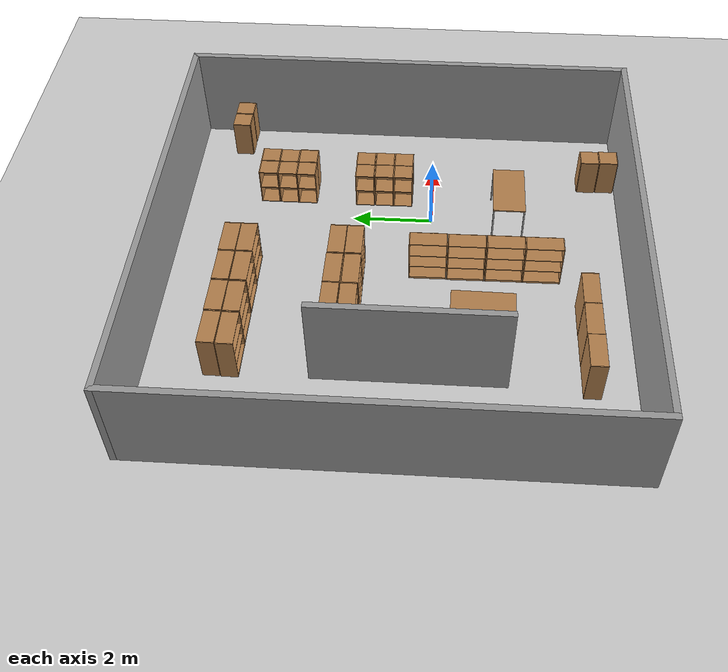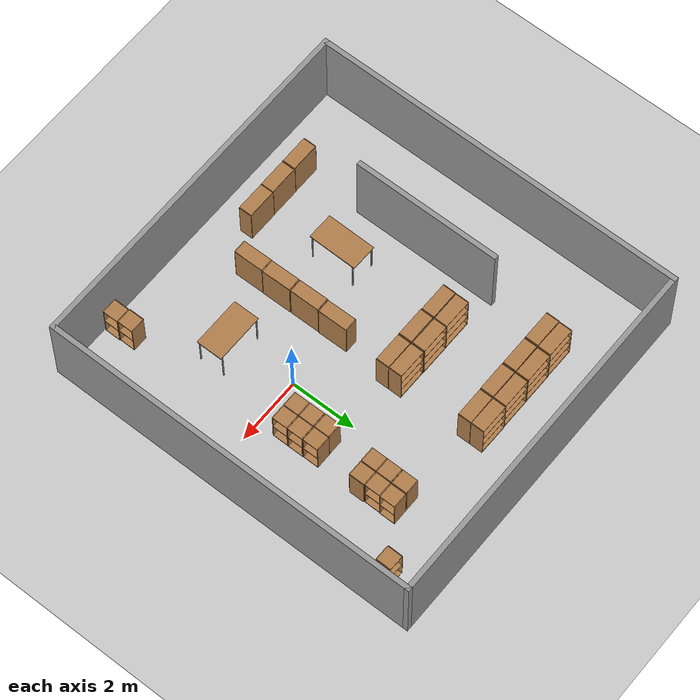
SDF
<sdf version="1.7">
 <world name="default">
  <light name="sun" type="directional">
   <pose>0 0 10 0 -0 0</pose>
   <diffuse>0.8 0.8 0.8 1</diffuse>
   <specular>0.2 0.2 0.2 1</specular>
   <attenuation>
    <range>1000</range>
    <constant>0.9</constant>
    <linear>0.01</linear>
    <quadratic>0.001</quadratic>
   </attenuation>
   <direction>-0.5 0.1 -0.9</direction>
   <spot><inner_angle>0</inner_angle><outer_angle>0</outer_angle><falloff>0</falloff></spot>
  </light>
  <model name="ground_plane">
   <static>1</static>
   <link name="link">
    <collision name="collision">
     <geometry><plane><normal>0 0 1</normal><size>100 100</size></plane></geometry>
     <surface>
      <contact><collide_bitmask>65535</collide_bitmask></contact>
      <friction><ode><mu>100</mu><mu2>50</mu2></ode></friction>
     </surface>
    </collision>
    <visual name="visual">
     <cast_shadows>0</cast_shadows>
     <geometry><plane><normal>0 0 1</normal><size>100 100</size></plane></geometry>
     <material>
      <script><uri>file://media/materials/scripts/gazebo.material</uri><name>Gazebo/Grey</name></script>
     </material>
    </visual>
   </link>
  </model>
  <physics type="ode">
   <real_time_update_rate>1000</real_time_update_rate>
   <max_step_size>0.001</max_step_size>
   <real_time_factor>1</real_time_factor>
   <ode>
    <solver>
     <type>quick</type>
     <iters>150</iters>
     <precon_iters>0</precon_iters>
     <sor>1.4</sor>
     <use_dynamic_moi_rescaling>1</use_dynamic_moi_rescaling>
    </solver>
    <constraints>
     <cfm>1e-05</cfm>
     <erp>0.2</erp>
     <contact_max_correcting_vel>2000</contact_max_correcting_vel>
     <contact_surface_layer>0.01</contact_surface_layer>
    </constraints>
   </ode>
  </physics>
  <scene><ambient>0.4 0.4 0.4 1</ambient><background>0.7 0.7 0.7 1</background><shadows>1</shadows></scene>
  <gravity>0 0 -9.8</gravity>
  <magnetic_field>6e-06 2.3e-05 -4.2e-05</magnetic_field>
  <atmosphere type="adiabatic"/>
  <spherical_coordinates>
   <surface_model>EARTH_WGS84</surface_model>
   <latitude_deg>0</latitude_deg>
   <longitude_deg>0</longitude_deg>
   <elevation>0</elevation>
   <heading_deg>0</heading_deg>
  </spherical_coordinates>
  <model name="BOUNDARY">
   <pose>-1.9849 0.78024 0 0 -0 0</pose>
   <link name="Wall_10">
    <collision name="Wall_10_Collision">
     <geometry><box><size>11 0.15 2.5</size></box></geometry>
     <pose>0 0 1.25 0 -0 0</pose>
    </collision>
    <visual name="Wall_10_Visual">
     <pose>0 0 1.25 0 -0 0</pose>
     <geometry><box><size>11 0.15 2.5</size></box></geometry>
     <material>
      <script><uri>file://media/materials/scripts/gazebo.material</uri><name>Gazebo/Grey</name></script>
      <ambient>1 1 1 1</ambient>
     </material>
     <meta><layer>0</layer></meta>
    </visual>
    <pose>-0 5.675 0 0 -0 3.14159</pose>
   </link>
   <link name="Wall_7">
    <collision name="Wall_7_Collision">
     <geometry><box><size>11.5 0.15 2.5</size></box></geometry>
     <pose>0 0 1.25 0 -0 0</pose>
    </collision>
    <visual name="Wall_7_Visual">
     <pose>0 0 1.25 0 -0 0</pose>
     <geometry><box><size>11.5 0.15 2.5</size></box></geometry>
     <material>
      <script><uri>file://media/materials/scripts/gazebo.material</uri><name>Gazebo/Grey</name></script>
      <ambient>1 1 1 1</ambient>
     </material>
     <meta><layer>0</layer></meta>
    </visual>
    <pose>-5.425 -0 0 0 -0 -1.5708</pose>
   </link>
   <link name="Wall_8">
    <collision name="Wall_8_Collision">
     <geometry><box><size>11 0.15 2.5</size></box></geometry>
     <pose>0 0 1.25 0 -0 0</pose>
    </collision>
    <visual name="Wall_8_Visual">
     <pose>0 0 1.25 0 -0 0</pose>
     <geometry><box><size>11 0.15 2.5</size></box></geometry>
     <material>
      <script><uri>file://media/materials/scripts/gazebo.material</uri><name>Gazebo/Grey</name></script>
      <ambient>1 1 1 1</ambient>
     </material>
     <meta><layer>0</layer></meta>
    </visual>
    <pose>-0 -5.675 0 0 -0 0</pose>
   </link>
   <link name="Wall_9">
    <collision name="Wall_9_Collision">
     <geometry><box><size>11.5 0.15 2.5</size></box></geometry>
     <pose>0 0 1.25 0 -0 0</pose>
    </collision>
    <visual name="Wall_9_Visual">
     <pose>0 0 1.25 0 -0 0</pose>
     <geometry><box><size>11.5 0.15 2.5</size></box></geometry>
     <material>
      <script><uri>file://media/materials/scripts/gazebo.material</uri><name>Gazebo/Grey</name></script>
      <ambient>1 1 1 1</ambient>
     </material>
     <meta><layer>0</layer></meta>
    </visual>
    <pose>5.425 -0 0 0 -0 1.5708</pose>
   </link>
   <static>1</static>
  </model>
  <model name="cabinet">
   <static>1</static>
   <link name="cabinet_bottom_plate">
    <inertial>
     <pose>0 0 -1 0 -0 0</pose>
     <inertia><ixx>2.05</ixx><ixy>0</ixy><ixz>0</ixz><iyy>2.05</iyy><iyz>0</iyz><izz>2.05</izz></inertia>
     <mass>25</mass>
    </inertial>
    <collision name="cabinet_bottom_plate_geom">
     <pose>0 0 0.01 0 -0 0</pose>
     <geometry><box><size>0.45 0.45 0.02</size></box></geometry>
    </collision>
    <visual name="cabinet_bottom_plate_geom_visual">
     <pose>0 0 0.01 0 -0 0</pose>
     <geometry><box><size>0.45 0.45 0.02</size></box></geometry>
     <material>
      <script><uri>file://media/materials/scripts/gazebo.material</uri><name>Gazebo/Wood</name></script>
     </material>
    </visual>
    <collision name="cabinet_bottom_plate_geom_cabinet_back_plate">
     <pose>0.235 0 0.51 0 -0 0</pose>
     <geometry><box><size>0.02 0.45 1.02</size></box></geometry>
    </collision>
    <visual name="cabinet_bottom_plate_geom_cabinet_back_plate_visual">
     <pose>0.235 0 0.51 0 -0 0</pose>
     <geometry><box><size>0.02 0.45 1.02</size></box></geometry>
     <material>
      <script><uri>file://media/materials/scripts/gazebo.material</uri><name>Gazebo/Wood</name></script>
     </material>
    </visual>
    <collision name="cabinet_bottom_plate_geom_cabinet_left_plate">
     <pose>0 0.235 0.51 0 -0 0</pose>
     <geometry><box><size>0.45 0.02 1.02</size></box></geometry>
    </collision>
    <visual name="cabinet_bottom_plate_geom_cabinet_left_plate_visual">
     <pose>0 0.235 0.51 0 -0 0</pose>
     <geometry><box><size>0.45 0.02 1.02</size></box></geometry>
     <material>
      <script><uri>file://media/materials/scripts/gazebo.material</uri><name>Gazebo/Wood</name></script>
     </material>
    </visual>
    <collision name="cabinet_bottom_plate_geom_cabinet_middle_plate">
     <pose>0 0 0.51 0 -0 0</pose>
     <geometry><box><size>0.45 0.45 0.02</size></box></geometry>
    </collision>
    <visual name="cabinet_bottom_plate_geom_cabinet_middle_plate_visual">
     <pose>0 0 0.51 0 -0 0</pose>
     <geometry><box><size>0.45 0.45 0.02</size></box></geometry>
     <material>
      <script><uri>file://media/materials/scripts/gazebo.material</uri><name>Gazebo/Wood</name></script>
     </material>
    </visual>
    <collision name="cabinet_bottom_plate_geom_cabinet_right_plate">
     <pose>0 -0.235 0.51 0 -0 0</pose>
     <geometry><box><size>0.45 0.02 1.02</size></box></geometry>
    </collision>
    <visual name="cabinet_bottom_plate_geom_cabinet_right_plate_visual">
     <pose>0 -0.235 0.51 0 -0 0</pose>
     <geometry><box><size>0.45 0.02 1.02</size></box></geometry>
     <material>
      <script><uri>file://media/materials/scripts/gazebo.material</uri><name>Gazebo/Wood</name></script>
     </material>
    </visual>
    <collision name="cabinet_bottom_plate_geom_cabinet_top_plate">
     <pose>0 0 1.01 0 -0 0</pose>
     <geometry><box><size>0.45 0.45 0.02</size></box></geometry>
    </collision>
    <visual name="cabinet_bottom_plate_geom_cabinet_top_plate_visual">
     <pose>0 0 1.01 0 -0 0</pose>
     <geometry><box><size>0.45 0.45 0.02</size></box></geometry>
     <material>
      <script><uri>file://media/materials/scripts/gazebo.material</uri><name>Gazebo/Wood</name></script>
     </material>
    </visual>
   </link>
   <pose>0.741021 4.23586 0 0 -0 0</pose>
  </model>
  <model name="cabinet_0">
   <static>1</static>
   <link name="cabinet_bottom_plate">
    <inertial>
     <pose>0 0 -1 0 -0 0</pose>
     <inertia><ixx>2.05</ixx><ixy>0</ixy><ixz>0</ixz><iyy>2.05</iyy><iyz>0</iyz><izz>2.05</izz></inertia>
     <mass>25</mass>
    </inertial>
    <collision name="cabinet_bottom_plate_geom">
     <pose>0 0 0.01 0 -0 0</pose>
     <geometry><box><size>0.45 0.45 0.02</size></box></geometry>
    </collision>
    <visual name="cabinet_bottom_plate_geom_visual">
     <pose>0 0 0.01 0 -0 0</pose>
     <geometry><box><size>0.45 0.45 0.02</size></box></geometry>
     <material>
      <script><uri>file://media/materials/scripts/gazebo.material</uri><name>Gazebo/Wood</name></script>
     </material>
    </visual>
    <collision name="cabinet_bottom_plate_geom_cabinet_back_plate">
     <pose>0.235 0 0.51 0 -0 0</pose>
     <geometry><box><size>0.02 0.45 1.02</size></box></geometry>
    </collision>
    <visual name="cabinet_bottom_plate_geom_cabinet_back_plate_visual">
     <pose>0.235 0 0.51 0 -0 0</pose>
     <geometry><box><size>0.02 0.45 1.02</size></box></geometry>
     <material>
      <script><uri>file://media/materials/scripts/gazebo.material</uri><name>Gazebo/Wood</name></script>
     </material>
    </visual>
    <collision name="cabinet_bottom_plate_geom_cabinet_left_plate">
     <pose>0 0.235 0.51 0 -0 0</pose>
     <geometry><box><size>0.45 0.02 1.02</size></box></geometry>
    </collision>
    <visual name="cabinet_bottom_plate_geom_cabinet_left_plate_visual">
     <pose>0 0.235 0.51 0 -0 0</pose>
     <geometry><box><size>0.45 0.02 1.02</size></box></geometry>
     <material>
      <script><uri>file://media/materials/scripts/gazebo.material</uri><name>Gazebo/Wood</name></script>
     </material>
    </visual>
    <collision name="cabinet_bottom_plate_geom_cabinet_middle_plate">
     <pose>0 0 0.51 0 -0 0</pose>
     <geometry><box><size>0.45 0.45 0.02</size></box></geometry>
    </collision>
    <visual name="cabinet_bottom_plate_geom_cabinet_middle_plate_visual">
     <pose>0 0 0.51 0 -0 0</pose>
     <geometry><box><size>0.45 0.45 0.02</size></box></geometry>
     <material>
      <script><uri>file://media/materials/scripts/gazebo.material</uri><name>Gazebo/Wood</name></script>
     </material>
    </visual>
    <collision name="cabinet_bottom_plate_geom_cabinet_right_plate">
     <pose>0 -0.235 0.51 0 -0 0</pose>
     <geometry><box><size>0.45 0.02 1.02</size></box></geometry>
    </collision>
    <visual name="cabinet_bottom_plate_geom_cabinet_right_plate_visual">
     <pose>0 -0.235 0.51 0 -0 0</pose>
     <geometry><box><size>0.45 0.02 1.02</size></box></geometry>
     <material>
      <script><uri>file://media/materials/scripts/gazebo.material</uri><name>Gazebo/Wood</name></script>
     </material>
    </visual>
    <collision name="cabinet_bottom_plate_geom_cabinet_top_plate">
     <pose>0 0 1.01 0 -0 0</pose>
     <geometry><box><size>0.45 0.45 0.02</size></box></geometry>
    </collision>
    <visual name="cabinet_bottom_plate_geom_cabinet_top_plate_visual">
     <pose>0 0 1.01 0 -0 0</pose>
     <geometry><box><size>0.45 0.45 0.02</size></box></geometry>
     <material>
      <script><uri>file://media/materials/scripts/gazebo.material</uri><name>Gazebo/Wood</name></script>
     </material>
    </visual>
   </link>
   <pose>0.740494 3.74263 0 0 -0 0</pose>
  </model>
  <model name="cabinet_1">
   <static>1</static>
   <link name="cabinet_bottom_plate">
    <inertial>
     <pose>0 0 -1 0 -0 0</pose>
     <inertia><ixx>2.05</ixx><ixy>0</ixy><ixz>0</ixz><iyy>2.05</iyy><iyz>0</iyz><izz>2.05</izz></inertia>
     <mass>25</mass>
    </inertial>
    <collision name="cabinet_bottom_plate_geom">
     <pose>0 0 0.01 0 -0 0</pose>
     <geometry><box><size>0.45 0.45 0.02</size></box></geometry>
    </collision>
    <visual name="cabinet_bottom_plate_geom_visual">
     <pose>0 0 0.01 0 -0 0</pose>
     <geometry><box><size>0.45 0.45 0.02</size></box></geometry>
     <material>
      <script><uri>file://media/materials/scripts/gazebo.material</uri><name>Gazebo/Wood</name></script>
     </material>
    </visual>
    <collision name="cabinet_bottom_plate_geom_cabinet_back_plate">
     <pose>0.235 0 0.51 0 -0 0</pose>
     <geometry><box><size>0.02 0.45 1.02</size></box></geometry>
    </collision>
    <visual name="cabinet_bottom_plate_geom_cabinet_back_plate_visual">
     <pose>0.235 0 0.51 0 -0 0</pose>
     <geometry><box><size>0.02 0.45 1.02</size></box></geometry>
     <material>
      <script><uri>file://media/materials/scripts/gazebo.material</uri><name>Gazebo/Wood</name></script>
     </material>
    </visual>
    <collision name="cabinet_bottom_plate_geom_cabinet_left_plate">
     <pose>0 0.235 0.51 0 -0 0</pose>
     <geometry><box><size>0.45 0.02 1.02</size></box></geometry>
    </collision>
    <visual name="cabinet_bottom_plate_geom_cabinet_left_plate_visual">
     <pose>0 0.235 0.51 0 -0 0</pose>
     <geometry><box><size>0.45 0.02 1.02</size></box></geometry>
     <material>
      <script><uri>file://media/materials/scripts/gazebo.material</uri><name>Gazebo/Wood</name></script>
     </material>
    </visual>
    <collision name="cabinet_bottom_plate_geom_cabinet_middle_plate">
     <pose>0 0 0.51 0 -0 0</pose>
     <geometry><box><size>0.45 0.45 0.02</size></box></geometry>
    </collision>
    <visual name="cabinet_bottom_plate_geom_cabinet_middle_plate_visual">
     <pose>0 0 0.51 0 -0 0</pose>
     <geometry><box><size>0.45 0.45 0.02</size></box></geometry>
     <material>
      <script><uri>file://media/materials/scripts/gazebo.material</uri><name>Gazebo/Wood</name></script>
     </material>
    </visual>
    <collision name="cabinet_bottom_plate_geom_cabinet_right_plate">
     <pose>0 -0.235 0.51 0 -0 0</pose>
     <geometry><box><size>0.45 0.02 1.02</size></box></geometry>
    </collision>
    <visual name="cabinet_bottom_plate_geom_cabinet_right_plate_visual">
     <pose>0 -0.235 0.51 0 -0 0</pose>
     <geometry><box><size>0.45 0.02 1.02</size></box></geometry>
     <material>
      <script><uri>file://media/materials/scripts/gazebo.material</uri><name>Gazebo/Wood</name></script>
     </material>
    </visual>
    <collision name="cabinet_bottom_plate_geom_cabinet_top_plate">
     <pose>0 0 1.01 0 -0 0</pose>
     <geometry><box><size>0.45 0.45 0.02</size></box></geometry>
    </collision>
    <visual name="cabinet_bottom_plate_geom_cabinet_top_plate_visual">
     <pose>0 0 1.01 0 -0 0</pose>
     <geometry><box><size>0.45 0.45 0.02</size></box></geometry>
     <material>
      <script><uri>file://media/materials/scripts/gazebo.material</uri><name>Gazebo/Wood</name></script>
     </material>
    </visual>
   </link>
   <pose>0.739877 3.25825 0 0 -0 0</pose>
  </model>
  <model name="cabinet_1_clone">
   <static>1</static>
   <link name="cabinet_bottom_plate">
    <inertial>
     <pose>0 0 -1 0 -0 0</pose>
     <inertia><ixx>2.05</ixx><ixy>0</ixy><ixz>0</ixz><iyy>2.05</iyy><iyz>0</iyz><izz>2.05</izz></inertia>
     <mass>25</mass>
    </inertial>
    <collision name="cabinet_bottom_plate_geom">
     <pose>0 0 0.01 0 -0 0</pose>
     <geometry><box><size>0.45 0.45 0.02</size></box></geometry>
    </collision>
    <visual name="cabinet_bottom_plate_geom_visual">
     <pose>0 0 0.01 0 -0 0</pose>
     <geometry><box><size>0.45 0.45 0.02</size></box></geometry>
     <material>
      <script><uri>file://media/materials/scripts/gazebo.material</uri><name>Gazebo/Wood</name></script>
     </material>
    </visual>
    <collision name="cabinet_bottom_plate_geom_cabinet_back_plate">
     <pose>0.235 0 0.51 0 -0 0</pose>
     <geometry><box><size>0.02 0.45 1.02</size></box></geometry>
    </collision>
    <visual name="cabinet_bottom_plate_geom_cabinet_back_plate_visual">
     <pose>0.235 0 0.51 0 -0 0</pose>
     <geometry><box><size>0.02 0.45 1.02</size></box></geometry>
     <material>
      <script><uri>file://media/materials/scripts/gazebo.material</uri><name>Gazebo/Wood</name></script>
     </material>
    </visual>
    <collision name="cabinet_bottom_plate_geom_cabinet_left_plate">
     <pose>0 0.235 0.51 0 -0 0</pose>
     <geometry><box><size>0.45 0.02 1.02</size></box></geometry>
    </collision>
    <visual name="cabinet_bottom_plate_geom_cabinet_left_plate_visual">
     <pose>0 0.235 0.51 0 -0 0</pose>
     <geometry><box><size>0.45 0.02 1.02</size></box></geometry>
     <material>
      <script><uri>file://media/materials/scripts/gazebo.material</uri><name>Gazebo/Wood</name></script>
     </material>
    </visual>
    <collision name="cabinet_bottom_plate_geom_cabinet_middle_plate">
     <pose>0 0 0.51 0 -0 0</pose>
     <geometry><box><size>0.45 0.45 0.02</size></box></geometry>
    </collision>
    <visual name="cabinet_bottom_plate_geom_cabinet_middle_plate_visual">
     <pose>0 0 0.51 0 -0 0</pose>
     <geometry><box><size>0.45 0.45 0.02</size></box></geometry>
     <material>
      <script><uri>file://media/materials/scripts/gazebo.material</uri><name>Gazebo/Wood</name></script>
     </material>
    </visual>
    <collision name="cabinet_bottom_plate_geom_cabinet_right_plate">
     <pose>0 -0.235 0.51 0 -0 0</pose>
     <geometry><box><size>0.45 0.02 1.02</size></box></geometry>
    </collision>
    <visual name="cabinet_bottom_plate_geom_cabinet_right_plate_visual">
     <pose>0 -0.235 0.51 0 -0 0</pose>
     <geometry><box><size>0.45 0.02 1.02</size></box></geometry>
     <material>
      <script><uri>file://media/materials/scripts/gazebo.material</uri><name>Gazebo/Wood</name></script>
     </material>
    </visual>
    <collision name="cabinet_bottom_plate_geom_cabinet_top_plate">
     <pose>0 0 1.01 0 -0 0</pose>
     <geometry><box><size>0.45 0.45 0.02</size></box></geometry>
    </collision>
    <visual name="cabinet_bottom_plate_geom_cabinet_top_plate_visual">
     <pose>0 0 1.01 0 -0 0</pose>
     <geometry><box><size>0.45 0.45 0.02</size></box></geometry>
     <material>
      <script><uri>file://media/materials/scripts/gazebo.material</uri><name>Gazebo/Wood</name></script>
     </material>
    </visual>
   </link>
   <pose>0.742442 1.74322 0 0 -0 0</pose>
  </model>
  <model name="cabinet_1_clone_0">
   <static>1</static>
   <link name="cabinet_bottom_plate">
    <inertial>
     <pose>0 0 -1 0 -0 0</pose>
     <inertia><ixx>2.05</ixx><ixy>0</ixy><ixz>0</ixz><iyy>2.05</iyy><iyz>0</iyz><izz>2.05</izz></inertia>
     <mass>25</mass>
    </inertial>
    <collision name="cabinet_bottom_plate_geom">
     <pose>0 0 0.01 0 -0 0</pose>
     <geometry><box><size>0.45 0.45 0.02</size></box></geometry>
    </collision>
    <visual name="cabinet_bottom_plate_geom_visual">
     <pose>0 0 0.01 0 -0 0</pose>
     <geometry><box><size>0.45 0.45 0.02</size></box></geometry>
     <material>
      <script><uri>file://media/materials/scripts/gazebo.material</uri><name>Gazebo/Wood</name></script>
     </material>
    </visual>
    <collision name="cabinet_bottom_plate_geom_cabinet_back_plate">
     <pose>0.235 0 0.51 0 -0 0</pose>
     <geometry><box><size>0.02 0.45 1.02</size></box></geometry>
    </collision>
    <visual name="cabinet_bottom_plate_geom_cabinet_back_plate_visual">
     <pose>0.235 0 0.51 0 -0 0</pose>
     <geometry><box><size>0.02 0.45 1.02</size></box></geometry>
     <material>
      <script><uri>file://media/materials/scripts/gazebo.material</uri><name>Gazebo/Wood</name></script>
     </material>
    </visual>
    <collision name="cabinet_bottom_plate_geom_cabinet_left_plate">
     <pose>0 0.235 0.51 0 -0 0</pose>
     <geometry><box><size>0.45 0.02 1.02</size></box></geometry>
    </collision>
    <visual name="cabinet_bottom_plate_geom_cabinet_left_plate_visual">
     <pose>0 0.235 0.51 0 -0 0</pose>
     <geometry><box><size>0.45 0.02 1.02</size></box></geometry>
     <material>
      <script><uri>file://media/materials/scripts/gazebo.material</uri><name>Gazebo/Wood</name></script>
     </material>
    </visual>
    <collision name="cabinet_bottom_plate_geom_cabinet_middle_plate">
     <pose>0 0 0.51 0 -0 0</pose>
     <geometry><box><size>0.45 0.45 0.02</size></box></geometry>
    </collision>
    <visual name="cabinet_bottom_plate_geom_cabinet_middle_plate_visual">
     <pose>0 0 0.51 0 -0 0</pose>
     <geometry><box><size>0.45 0.45 0.02</size></box></geometry>
     <material>
      <script><uri>file://media/materials/scripts/gazebo.material</uri><name>Gazebo/Wood</name></script>
     </material>
    </visual>
    <collision name="cabinet_bottom_plate_geom_cabinet_right_plate">
     <pose>0 -0.235 0.51 0 -0 0</pose>
     <geometry><box><size>0.45 0.02 1.02</size></box></geometry>
    </collision>
    <visual name="cabinet_bottom_plate_geom_cabinet_right_plate_visual">
     <pose>0 -0.235 0.51 0 -0 0</pose>
     <geometry><box><size>0.45 0.02 1.02</size></box></geometry>
     <material>
      <script><uri>file://media/materials/scripts/gazebo.material</uri><name>Gazebo/Wood</name></script>
     </material>
    </visual>
    <collision name="cabinet_bottom_plate_geom_cabinet_top_plate">
     <pose>0 0 1.01 0 -0 0</pose>
     <geometry><box><size>0.45 0.45 0.02</size></box></geometry>
    </collision>
    <visual name="cabinet_bottom_plate_geom_cabinet_top_plate_visual">
     <pose>0 0 1.01 0 -0 0</pose>
     <geometry><box><size>0.45 0.45 0.02</size></box></geometry>
     <material>
      <script><uri>file://media/materials/scripts/gazebo.material</uri><name>Gazebo/Wood</name></script>
     </material>
    </visual>
   </link>
   <pose>0.750838 1.24697 0 0 -0 0</pose>
  </model>
  <model name="cabinet_1_clone_1">
   <static>1</static>
   <link name="cabinet_bottom_plate">
    <inertial>
     <pose>0 0 -1 0 -0 0</pose>
     <inertia><ixx>2.05</ixx><ixy>0</ixy><ixz>0</ixz><iyy>2.05</iyy><iyz>0</iyz><izz>2.05</izz></inertia>
     <mass>25</mass>
    </inertial>
    <collision name="cabinet_bottom_plate_geom">
     <pose>0 0 0.01 0 -0 0</pose>
     <geometry><box><size>0.45 0.45 0.02</size></box></geometry>
    </collision>
    <visual name="cabinet_bottom_plate_geom_visual">
     <pose>0 0 0.01 0 -0 0</pose>
     <geometry><box><size>0.45 0.45 0.02</size></box></geometry>
     <material>
      <script><uri>file://media/materials/scripts/gazebo.material</uri><name>Gazebo/Wood</name></script>
     </material>
    </visual>
    <collision name="cabinet_bottom_plate_geom_cabinet_back_plate">
     <pose>0.235 0 0.51 0 -0 0</pose>
     <geometry><box><size>0.02 0.45 1.02</size></box></geometry>
    </collision>
    <visual name="cabinet_bottom_plate_geom_cabinet_back_plate_visual">
     <pose>0.235 0 0.51 0 -0 0</pose>
     <geometry><box><size>0.02 0.45 1.02</size></box></geometry>
     <material>
      <script><uri>file://media/materials/scripts/gazebo.material</uri><name>Gazebo/Wood</name></script>
     </material>
    </visual>
    <collision name="cabinet_bottom_plate_geom_cabinet_left_plate">
     <pose>0 0.235 0.51 0 -0 0</pose>
     <geometry><box><size>0.45 0.02 1.02</size></box></geometry>
    </collision>
    <visual name="cabinet_bottom_plate_geom_cabinet_left_plate_visual">
     <pose>0 0.235 0.51 0 -0 0</pose>
     <geometry><box><size>0.45 0.02 1.02</size></box></geometry>
     <material>
      <script><uri>file://media/materials/scripts/gazebo.material</uri><name>Gazebo/Wood</name></script>
     </material>
    </visual>
    <collision name="cabinet_bottom_plate_geom_cabinet_middle_plate">
     <pose>0 0 0.51 0 -0 0</pose>
     <geometry><box><size>0.45 0.45 0.02</size></box></geometry>
    </collision>
    <visual name="cabinet_bottom_plate_geom_cabinet_middle_plate_visual">
     <pose>0 0 0.51 0 -0 0</pose>
     <geometry><box><size>0.45 0.45 0.02</size></box></geometry>
     <material>
      <script><uri>file://media/materials/scripts/gazebo.material</uri><name>Gazebo/Wood</name></script>
     </material>
    </visual>
    <collision name="cabinet_bottom_plate_geom_cabinet_right_plate">
     <pose>0 -0.235 0.51 0 -0 0</pose>
     <geometry><box><size>0.45 0.02 1.02</size></box></geometry>
    </collision>
    <visual name="cabinet_bottom_plate_geom_cabinet_right_plate_visual">
     <pose>0 -0.235 0.51 0 -0 0</pose>
     <geometry><box><size>0.45 0.02 1.02</size></box></geometry>
     <material>
      <script><uri>file://media/materials/scripts/gazebo.material</uri><name>Gazebo/Wood</name></script>
     </material>
    </visual>
    <collision name="cabinet_bottom_plate_geom_cabinet_top_plate">
     <pose>0 0 1.01 0 -0 0</pose>
     <geometry><box><size>0.45 0.45 0.02</size></box></geometry>
    </collision>
    <visual name="cabinet_bottom_plate_geom_cabinet_top_plate_visual">
     <pose>0 0 1.01 0 -0 0</pose>
     <geometry><box><size>0.45 0.45 0.02</size></box></geometry>
     <material>
      <script><uri>file://media/materials/scripts/gazebo.material</uri><name>Gazebo/Wood</name></script>
     </material>
    </visual>
   </link>
   <pose>0.754546 0.758666 0 0 -0 0</pose>
  </model>
  <model name="cabinet_clone">
   <static>1</static>
   <link name="cabinet_bottom_plate">
    <inertial>
     <pose>0 0 -1 0 -0 0</pose>
     <inertia><ixx>2.05</ixx><ixy>0</ixy><ixz>0</ixz><iyy>2.05</iyy><iyz>0</iyz><izz>2.05</izz></inertia>
     <mass>25</mass>
    </inertial>
    <collision name="cabinet_bottom_plate_geom">
     <pose>0 0 0.01 0 -0 0</pose>
     <geometry><box><size>0.45 0.45 0.02</size></box></geometry>
    </collision>
    <visual name="cabinet_bottom_plate_geom_visual">
     <pose>0 0 0.01 0 -0 0</pose>
     <geometry><box><size>0.45 0.45 0.02</size></box></geometry>
     <material>
      <script><uri>file://media/materials/scripts/gazebo.material</uri><name>Gazebo/Wood</name></script>
     </material>
    </visual>
    <collision name="cabinet_bottom_plate_geom_cabinet_back_plate">
     <pose>0.235 0 0.51 0 -0 0</pose>
     <geometry><box><size>0.02 0.45 1.02</size></box></geometry>
    </collision>
    <visual name="cabinet_bottom_plate_geom_cabinet_back_plate_visual">
     <pose>0.235 0 0.51 0 -0 0</pose>
     <geometry><box><size>0.02 0.45 1.02</size></box></geometry>
     <material>
      <script><uri>file://media/materials/scripts/gazebo.material</uri><name>Gazebo/Wood</name></script>
     </material>
    </visual>
    <collision name="cabinet_bottom_plate_geom_cabinet_left_plate">
     <pose>0 0.235 0.51 0 -0 0</pose>
     <geometry><box><size>0.45 0.02 1.02</size></box></geometry>
    </collision>
    <visual name="cabinet_bottom_plate_geom_cabinet_left_plate_visual">
     <pose>0 0.235 0.51 0 -0 0</pose>
     <geometry><box><size>0.45 0.02 1.02</size></box></geometry>
     <material>
      <script><uri>file://media/materials/scripts/gazebo.material</uri><name>Gazebo/Wood</name></script>
     </material>
    </visual>
    <collision name="cabinet_bottom_plate_geom_cabinet_middle_plate">
     <pose>0 0 0.51 0 -0 0</pose>
     <geometry><box><size>0.45 0.45 0.02</size></box></geometry>
    </collision>
    <visual name="cabinet_bottom_plate_geom_cabinet_middle_plate_visual">
     <pose>0 0 0.51 0 -0 0</pose>
     <geometry><box><size>0.45 0.45 0.02</size></box></geometry>
     <material>
      <script><uri>file://media/materials/scripts/gazebo.material</uri><name>Gazebo/Wood</name></script>
     </material>
    </visual>
    <collision name="cabinet_bottom_plate_geom_cabinet_right_plate">
     <pose>0 -0.235 0.51 0 -0 0</pose>
     <geometry><box><size>0.45 0.02 1.02</size></box></geometry>
    </collision>
    <visual name="cabinet_bottom_plate_geom_cabinet_right_plate_visual">
     <pose>0 -0.235 0.51 0 -0 0</pose>
     <geometry><box><size>0.45 0.02 1.02</size></box></geometry>
     <material>
      <script><uri>file://media/materials/scripts/gazebo.material</uri><name>Gazebo/Wood</name></script>
     </material>
    </visual>
    <collision name="cabinet_bottom_plate_geom_cabinet_top_plate">
     <pose>0 0 1.01 0 -0 0</pose>
     <geometry><box><size>0.45 0.45 0.02</size></box></geometry>
    </collision>
    <visual name="cabinet_bottom_plate_geom_cabinet_top_plate_visual">
     <pose>0 0 1.01 0 -0 0</pose>
     <geometry><box><size>0.45 0.45 0.02</size></box></geometry>
     <material>
      <script><uri>file://media/materials/scripts/gazebo.material</uri><name>Gazebo/Wood</name></script>
     </material>
    </visual>
   </link>
   <pose>3.09381 5.21485 0 0 0 -1.58352</pose>
  </model>
  <model name="cabinet_clone_clone">
   <static>1</static>
   <link name="cabinet_bottom_plate">
    <inertial>
     <pose>0 0 -1 0 -0 0</pose>
     <inertia><ixx>2.05</ixx><ixy>0</ixy><ixz>0</ixz><iyy>2.05</iyy><iyz>0</iyz><izz>2.05</izz></inertia>
     <mass>25</mass>
    </inertial>
    <collision name="cabinet_bottom_plate_geom">
     <pose>0 0 0.01 0 -0 0</pose>
     <geometry><box><size>0.45 0.45 0.02</size></box></geometry>
    </collision>
    <visual name="cabinet_bottom_plate_geom_visual">
     <pose>0 0 0.01 0 -0 0</pose>
     <geometry><box><size>0.45 0.45 0.02</size></box></geometry>
     <material>
      <script><uri>file://media/materials/scripts/gazebo.material</uri><name>Gazebo/Wood</name></script>
     </material>
    </visual>
    <collision name="cabinet_bottom_plate_geom_cabinet_back_plate">
     <pose>0.235 0 0.51 0 -0 0</pose>
     <geometry><box><size>0.02 0.45 1.02</size></box></geometry>
    </collision>
    <visual name="cabinet_bottom_plate_geom_cabinet_back_plate_visual">
     <pose>0.235 0 0.51 0 -0 0</pose>
     <geometry><box><size>0.02 0.45 1.02</size></box></geometry>
     <material>
      <script><uri>file://media/materials/scripts/gazebo.material</uri><name>Gazebo/Wood</name></script>
     </material>
    </visual>
    <collision name="cabinet_bottom_plate_geom_cabinet_left_plate">
     <pose>0 0.235 0.51 0 -0 0</pose>
     <geometry><box><size>0.45 0.02 1.02</size></box></geometry>
    </collision>
    <visual name="cabinet_bottom_plate_geom_cabinet_left_plate_visual">
     <pose>0 0.235 0.51 0 -0 0</pose>
     <geometry><box><size>0.45 0.02 1.02</size></box></geometry>
     <material>
      <script><uri>file://media/materials/scripts/gazebo.material</uri><name>Gazebo/Wood</name></script>
     </material>
    </visual>
    <collision name="cabinet_bottom_plate_geom_cabinet_middle_plate">
     <pose>0 0 0.51 0 -0 0</pose>
     <geometry><box><size>0.45 0.45 0.02</size></box></geometry>
    </collision>
    <visual name="cabinet_bottom_plate_geom_cabinet_middle_plate_visual">
     <pose>0 0 0.51 0 -0 0</pose>
     <geometry><box><size>0.45 0.45 0.02</size></box></geometry>
     <material>
      <script><uri>file://media/materials/scripts/gazebo.material</uri><name>Gazebo/Wood</name></script>
     </material>
    </visual>
    <collision name="cabinet_bottom_plate_geom_cabinet_right_plate">
     <pose>0 -0.235 0.51 0 -0 0</pose>
     <geometry><box><size>0.45 0.02 1.02</size></box></geometry>
    </collision>
    <visual name="cabinet_bottom_plate_geom_cabinet_right_plate_visual">
     <pose>0 -0.235 0.51 0 -0 0</pose>
     <geometry><box><size>0.45 0.02 1.02</size></box></geometry>
     <material>
      <script><uri>file://media/materials/scripts/gazebo.material</uri><name>Gazebo/Wood</name></script>
     </material>
    </visual>
    <collision name="cabinet_bottom_plate_geom_cabinet_top_plate">
     <pose>0 0 1.01 0 -0 0</pose>
     <geometry><box><size>0.45 0.45 0.02</size></box></geometry>
    </collision>
    <visual name="cabinet_bottom_plate_geom_cabinet_top_plate_visual">
     <pose>0 0 1.01 0 -0 0</pose>
     <geometry><box><size>0.45 0.45 0.02</size></box></geometry>
     <material>
      <script><uri>file://media/materials/scripts/gazebo.material</uri><name>Gazebo/Wood</name></script>
     </material>
    </visual>
   </link>
   <pose>2.60288 5.22368 0 0 0 -1.58352</pose>
  </model>
  <model name="cabinet_clone_0">
   <static>1</static>
   <link name="cabinet_bottom_plate">
    <inertial>
     <pose>0 0 -1 0 -0 0</pose>
     <inertia><ixx>2.05</ixx><ixy>0</ixy><ixz>0</ixz><iyy>2.05</iyy><iyz>0</iyz><izz>2.05</izz></inertia>
     <mass>25</mass>
    </inertial>
    <collision name="cabinet_bottom_plate_geom">
     <pose>0 0 0.01 0 -0 0</pose>
     <geometry><box><size>0.45 0.45 0.02</size></box></geometry>
    </collision>
    <visual name="cabinet_bottom_plate_geom_visual">
     <pose>0 0 0.01 0 -0 0</pose>
     <geometry><box><size>0.45 0.45 0.02</size></box></geometry>
     <material>
      <script><uri>file://media/materials/scripts/gazebo.material</uri><name>Gazebo/Wood</name></script>
     </material>
    </visual>
    <collision name="cabinet_bottom_plate_geom_cabinet_back_plate">
     <pose>0.235 0 0.51 0 -0 0</pose>
     <geometry><box><size>0.02 0.45 1.02</size></box></geometry>
    </collision>
    <visual name="cabinet_bottom_plate_geom_cabinet_back_plate_visual">
     <pose>0.235 0 0.51 0 -0 0</pose>
     <geometry><box><size>0.02 0.45 1.02</size></box></geometry>
     <material>
      <script><uri>file://media/materials/scripts/gazebo.material</uri><name>Gazebo/Wood</name></script>
     </material>
    </visual>
    <collision name="cabinet_bottom_plate_geom_cabinet_left_plate">
     <pose>0 0.235 0.51 0 -0 0</pose>
     <geometry><box><size>0.45 0.02 1.02</size></box></geometry>
    </collision>
    <visual name="cabinet_bottom_plate_geom_cabinet_left_plate_visual">
     <pose>0 0.235 0.51 0 -0 0</pose>
     <geometry><box><size>0.45 0.02 1.02</size></box></geometry>
     <material>
      <script><uri>file://media/materials/scripts/gazebo.material</uri><name>Gazebo/Wood</name></script>
     </material>
    </visual>
    <collision name="cabinet_bottom_plate_geom_cabinet_middle_plate">
     <pose>0 0 0.51 0 -0 0</pose>
     <geometry><box><size>0.45 0.45 0.02</size></box></geometry>
    </collision>
    <visual name="cabinet_bottom_plate_geom_cabinet_middle_plate_visual">
     <pose>0 0 0.51 0 -0 0</pose>
     <geometry><box><size>0.45 0.45 0.02</size></box></geometry>
     <material>
      <script><uri>file://media/materials/scripts/gazebo.material</uri><name>Gazebo/Wood</name></script>
     </material>
    </visual>
    <collision name="cabinet_bottom_plate_geom_cabinet_right_plate">
     <pose>0 -0.235 0.51 0 -0 0</pose>
     <geometry><box><size>0.45 0.02 1.02</size></box></geometry>
    </collision>
    <visual name="cabinet_bottom_plate_geom_cabinet_right_plate_visual">
     <pose>0 -0.235 0.51 0 -0 0</pose>
     <geometry><box><size>0.45 0.02 1.02</size></box></geometry>
     <material>
      <script><uri>file://media/materials/scripts/gazebo.material</uri><name>Gazebo/Wood</name></script>
     </material>
    </visual>
    <collision name="cabinet_bottom_plate_geom_cabinet_top_plate">
     <pose>0 0 1.01 0 -0 0</pose>
     <geometry><box><size>0.45 0.45 0.02</size></box></geometry>
    </collision>
    <visual name="cabinet_bottom_plate_geom_cabinet_top_plate_visual">
     <pose>0 0 1.01 0 -0 0</pose>
     <geometry><box><size>0.45 0.45 0.02</size></box></geometry>
     <material>
      <script><uri>file://media/materials/scripts/gazebo.material</uri><name>Gazebo/Wood</name></script>
     </material>
    </visual>
   </link>
   <pose>1.22598 4.23696 0 0 0 -3.14016</pose>
  </model>
  <model name="cabinet_clone_1">
   <static>1</static>
   <link name="cabinet_bottom_plate">
    <inertial>
     <pose>0 0 -1 0 -0 0</pose>
     <inertia><ixx>2.05</ixx><ixy>0</ixy><ixz>0</ixz><iyy>2.05</iyy><iyz>0</iyz><izz>2.05</izz></inertia>
     <mass>25</mass>
    </inertial>
    <collision name="cabinet_bottom_plate_geom">
     <pose>0 0 0.01 0 -0 0</pose>
     <geometry><box><size>0.45 0.45 0.02</size></box></geometry>
    </collision>
    <visual name="cabinet_bottom_plate_geom_visual">
     <pose>0 0 0.01 0 -0 0</pose>
     <geometry><box><size>0.45 0.45 0.02</size></box></geometry>
     <material>
      <script><uri>file://media/materials/scripts/gazebo.material</uri><name>Gazebo/Wood</name></script>
     </material>
    </visual>
    <collision name="cabinet_bottom_plate_geom_cabinet_back_plate">
     <pose>0.235 0 0.51 0 -0 0</pose>
     <geometry><box><size>0.02 0.45 1.02</size></box></geometry>
    </collision>
    <visual name="cabinet_bottom_plate_geom_cabinet_back_plate_visual">
     <pose>0.235 0 0.51 0 -0 0</pose>
     <geometry><box><size>0.02 0.45 1.02</size></box></geometry>
     <material>
      <script><uri>file://media/materials/scripts/gazebo.material</uri><name>Gazebo/Wood</name></script>
     </material>
    </visual>
    <collision name="cabinet_bottom_plate_geom_cabinet_left_plate">
     <pose>0 0.235 0.51 0 -0 0</pose>
     <geometry><box><size>0.45 0.02 1.02</size></box></geometry>
    </collision>
    <visual name="cabinet_bottom_plate_geom_cabinet_left_plate_visual">
     <pose>0 0.235 0.51 0 -0 0</pose>
     <geometry><box><size>0.45 0.02 1.02</size></box></geometry>
     <material>
      <script><uri>file://media/materials/scripts/gazebo.material</uri><name>Gazebo/Wood</name></script>
     </material>
    </visual>
    <collision name="cabinet_bottom_plate_geom_cabinet_middle_plate">
     <pose>0 0 0.51 0 -0 0</pose>
     <geometry><box><size>0.45 0.45 0.02</size></box></geometry>
    </collision>
    <visual name="cabinet_bottom_plate_geom_cabinet_middle_plate_visual">
     <pose>0 0 0.51 0 -0 0</pose>
     <geometry><box><size>0.45 0.45 0.02</size></box></geometry>
     <material>
      <script><uri>file://media/materials/scripts/gazebo.material</uri><name>Gazebo/Wood</name></script>
     </material>
    </visual>
    <collision name="cabinet_bottom_plate_geom_cabinet_right_plate">
     <pose>0 -0.235 0.51 0 -0 0</pose>
     <geometry><box><size>0.45 0.02 1.02</size></box></geometry>
    </collision>
    <visual name="cabinet_bottom_plate_geom_cabinet_right_plate_visual">
     <pose>0 -0.235 0.51 0 -0 0</pose>
     <geometry><box><size>0.45 0.02 1.02</size></box></geometry>
     <material>
      <script><uri>file://media/materials/scripts/gazebo.material</uri><name>Gazebo/Wood</name></script>
     </material>
    </visual>
    <collision name="cabinet_bottom_plate_geom_cabinet_top_plate">
     <pose>0 0 1.01 0 -0 0</pose>
     <geometry><box><size>0.45 0.45 0.02</size></box></geometry>
    </collision>
    <visual name="cabinet_bottom_plate_geom_cabinet_top_plate_visual">
     <pose>0 0 1.01 0 -0 0</pose>
     <geometry><box><size>0.45 0.45 0.02</size></box></geometry>
     <material>
      <script><uri>file://media/materials/scripts/gazebo.material</uri><name>Gazebo/Wood</name></script>
     </material>
    </visual>
   </link>
   <pose>1.2155 3.75232 0 0 -0 3.13868</pose>
  </model>
  <model name="cabinet_clone_2">
   <static>1</static>
   <link name="cabinet_bottom_plate">
    <inertial>
     <pose>0 0 -1 0 -0 0</pose>
     <inertia><ixx>2.05</ixx><ixy>0</ixy><ixz>0</ixz><iyy>2.05</iyy><iyz>0</iyz><izz>2.05</izz></inertia>
     <mass>25</mass>
    </inertial>
    <collision name="cabinet_bottom_plate_geom">
     <pose>0 0 0.01 0 -0 0</pose>
     <geometry><box><size>0.45 0.45 0.02</size></box></geometry>
    </collision>
    <visual name="cabinet_bottom_plate_geom_visual">
     <pose>0 0 0.01 0 -0 0</pose>
     <geometry><box><size>0.45 0.45 0.02</size></box></geometry>
     <material>
      <script><uri>file://media/materials/scripts/gazebo.material</uri><name>Gazebo/Wood</name></script>
     </material>
    </visual>
    <collision name="cabinet_bottom_plate_geom_cabinet_back_plate">
     <pose>0.235 0 0.51 0 -0 0</pose>
     <geometry><box><size>0.02 0.45 1.02</size></box></geometry>
    </collision>
    <visual name="cabinet_bottom_plate_geom_cabinet_back_plate_visual">
     <pose>0.235 0 0.51 0 -0 0</pose>
     <geometry><box><size>0.02 0.45 1.02</size></box></geometry>
     <material>
      <script><uri>file://media/materials/scripts/gazebo.material</uri><name>Gazebo/Wood</name></script>
     </material>
    </visual>
    <collision name="cabinet_bottom_plate_geom_cabinet_left_plate">
     <pose>0 0.235 0.51 0 -0 0</pose>
     <geometry><box><size>0.45 0.02 1.02</size></box></geometry>
    </collision>
    <visual name="cabinet_bottom_plate_geom_cabinet_left_plate_visual">
     <pose>0 0.235 0.51 0 -0 0</pose>
     <geometry><box><size>0.45 0.02 1.02</size></box></geometry>
     <material>
      <script><uri>file://media/materials/scripts/gazebo.material</uri><name>Gazebo/Wood</name></script>
     </material>
    </visual>
    <collision name="cabinet_bottom_plate_geom_cabinet_middle_plate">
     <pose>0 0 0.51 0 -0 0</pose>
     <geometry><box><size>0.45 0.45 0.02</size></box></geometry>
    </collision>
    <visual name="cabinet_bottom_plate_geom_cabinet_middle_plate_visual">
     <pose>0 0 0.51 0 -0 0</pose>
     <geometry><box><size>0.45 0.45 0.02</size></box></geometry>
     <material>
      <script><uri>file://media/materials/scripts/gazebo.material</uri><name>Gazebo/Wood</name></script>
     </material>
    </visual>
    <collision name="cabinet_bottom_plate_geom_cabinet_right_plate">
     <pose>0 -0.235 0.51 0 -0 0</pose>
     <geometry><box><size>0.45 0.02 1.02</size></box></geometry>
    </collision>
    <visual name="cabinet_bottom_plate_geom_cabinet_right_plate_visual">
     <pose>0 -0.235 0.51 0 -0 0</pose>
     <geometry><box><size>0.45 0.02 1.02</size></box></geometry>
     <material>
      <script><uri>file://media/materials/scripts/gazebo.material</uri><name>Gazebo/Wood</name></script>
     </material>
    </visual>
    <collision name="cabinet_bottom_plate_geom_cabinet_top_plate">
     <pose>0 0 1.01 0 -0 0</pose>
     <geometry><box><size>0.45 0.45 0.02</size></box></geometry>
    </collision>
    <visual name="cabinet_bottom_plate_geom_cabinet_top_plate_visual">
     <pose>0 0 1.01 0 -0 0</pose>
     <geometry><box><size>0.45 0.45 0.02</size></box></geometry>
     <material>
      <script><uri>file://media/materials/scripts/gazebo.material</uri><name>Gazebo/Wood</name></script>
     </material>
    </visual>
   </link>
   <pose>1.21847 3.26248 0 0 -0 0</pose>
  </model>
  <model name="cabinet_clone_2_clone">
   <static>1</static>
   <link name="cabinet_bottom_plate">
    <inertial>
     <pose>0 0 -1 0 -0 0</pose>
     <inertia><ixx>2.05</ixx><ixy>0</ixy><ixz>0</ixz><iyy>2.05</iyy><iyz>0</iyz><izz>2.05</izz></inertia>
     <mass>25</mass>
    </inertial>
    <collision name="cabinet_bottom_plate_geom">
     <pose>0 0 0.01 0 -0 0</pose>
     <geometry><box><size>0.45 0.45 0.02</size></box></geometry>
    </collision>
    <visual name="cabinet_bottom_plate_geom_visual">
     <pose>0 0 0.01 0 -0 0</pose>
     <geometry><box><size>0.45 0.45 0.02</size></box></geometry>
     <material>
      <script><uri>file://media/materials/scripts/gazebo.material</uri><name>Gazebo/Wood</name></script>
     </material>
    </visual>
    <collision name="cabinet_bottom_plate_geom_cabinet_back_plate">
     <pose>0.235 0 0.51 0 -0 0</pose>
     <geometry><box><size>0.02 0.45 1.02</size></box></geometry>
    </collision>
    <visual name="cabinet_bottom_plate_geom_cabinet_back_plate_visual">
     <pose>0.235 0 0.51 0 -0 0</pose>
     <geometry><box><size>0.02 0.45 1.02</size></box></geometry>
     <material>
      <script><uri>file://media/materials/scripts/gazebo.material</uri><name>Gazebo/Wood</name></script>
     </material>
    </visual>
    <collision name="cabinet_bottom_plate_geom_cabinet_left_plate">
     <pose>0 0.235 0.51 0 -0 0</pose>
     <geometry><box><size>0.45 0.02 1.02</size></box></geometry>
    </collision>
    <visual name="cabinet_bottom_plate_geom_cabinet_left_plate_visual">
     <pose>0 0.235 0.51 0 -0 0</pose>
     <geometry><box><size>0.45 0.02 1.02</size></box></geometry>
     <material>
      <script><uri>file://media/materials/scripts/gazebo.material</uri><name>Gazebo/Wood</name></script>
     </material>
    </visual>
    <collision name="cabinet_bottom_plate_geom_cabinet_middle_plate">
     <pose>0 0 0.51 0 -0 0</pose>
     <geometry><box><size>0.45 0.45 0.02</size></box></geometry>
    </collision>
    <visual name="cabinet_bottom_plate_geom_cabinet_middle_plate_visual">
     <pose>0 0 0.51 0 -0 0</pose>
     <geometry><box><size>0.45 0.45 0.02</size></box></geometry>
     <material>
      <script><uri>file://media/materials/scripts/gazebo.material</uri><name>Gazebo/Wood</name></script>
     </material>
    </visual>
    <collision name="cabinet_bottom_plate_geom_cabinet_right_plate">
     <pose>0 -0.235 0.51 0 -0 0</pose>
     <geometry><box><size>0.45 0.02 1.02</size></box></geometry>
    </collision>
    <visual name="cabinet_bottom_plate_geom_cabinet_right_plate_visual">
     <pose>0 -0.235 0.51 0 -0 0</pose>
     <geometry><box><size>0.45 0.02 1.02</size></box></geometry>
     <material>
      <script><uri>file://media/materials/scripts/gazebo.material</uri><name>Gazebo/Wood</name></script>
     </material>
    </visual>
    <collision name="cabinet_bottom_plate_geom_cabinet_top_plate">
     <pose>0 0 1.01 0 -0 0</pose>
     <geometry><box><size>0.45 0.45 0.02</size></box></geometry>
    </collision>
    <visual name="cabinet_bottom_plate_geom_cabinet_top_plate_visual">
     <pose>0 0 1.01 0 -0 0</pose>
     <geometry><box><size>0.45 0.45 0.02</size></box></geometry>
     <material>
      <script><uri>file://media/materials/scripts/gazebo.material</uri><name>Gazebo/Wood</name></script>
     </material>
    </visual>
   </link>
   <pose>1.21144 1.75069 0 0 -0 3.14114</pose>
  </model>
  <model name="cabinet_clone_2_clone_clone">
   <static>1</static>
   <link name="cabinet_bottom_plate">
    <inertial>
     <pose>0 0 -1 0 -0 0</pose>
     <inertia><ixx>2.05</ixx><ixy>0</ixy><ixz>0</ixz><iyy>2.05</iyy><iyz>0</iyz><izz>2.05</izz></inertia>
     <mass>25</mass>
    </inertial>
    <collision name="cabinet_bottom_plate_geom">
     <pose>0 0 0.01 0 -0 0</pose>
     <geometry><box><size>0.45 0.45 0.02</size></box></geometry>
    </collision>
    <visual name="cabinet_bottom_plate_geom_visual">
     <pose>0 0 0.01 0 -0 0</pose>
     <geometry><box><size>0.45 0.45 0.02</size></box></geometry>
     <material>
      <script><uri>file://media/materials/scripts/gazebo.material</uri><name>Gazebo/Wood</name></script>
     </material>
    </visual>
    <collision name="cabinet_bottom_plate_geom_cabinet_back_plate">
     <pose>0.235 0 0.51 0 -0 0</pose>
     <geometry><box><size>0.02 0.45 1.02</size></box></geometry>
    </collision>
    <visual name="cabinet_bottom_plate_geom_cabinet_back_plate_visual">
     <pose>0.235 0 0.51 0 -0 0</pose>
     <geometry><box><size>0.02 0.45 1.02</size></box></geometry>
     <material>
      <script><uri>file://media/materials/scripts/gazebo.material</uri><name>Gazebo/Wood</name></script>
     </material>
    </visual>
    <collision name="cabinet_bottom_plate_geom_cabinet_left_plate">
     <pose>0 0.235 0.51 0 -0 0</pose>
     <geometry><box><size>0.45 0.02 1.02</size></box></geometry>
    </collision>
    <visual name="cabinet_bottom_plate_geom_cabinet_left_plate_visual">
     <pose>0 0.235 0.51 0 -0 0</pose>
     <geometry><box><size>0.45 0.02 1.02</size></box></geometry>
     <material>
      <script><uri>file://media/materials/scripts/gazebo.material</uri><name>Gazebo/Wood</name></script>
     </material>
    </visual>
    <collision name="cabinet_bottom_plate_geom_cabinet_middle_plate">
     <pose>0 0 0.51 0 -0 0</pose>
     <geometry><box><size>0.45 0.45 0.02</size></box></geometry>
    </collision>
    <visual name="cabinet_bottom_plate_geom_cabinet_middle_plate_visual">
     <pose>0 0 0.51 0 -0 0</pose>
     <geometry><box><size>0.45 0.45 0.02</size></box></geometry>
     <material>
      <script><uri>file://media/materials/scripts/gazebo.material</uri><name>Gazebo/Wood</name></script>
     </material>
    </visual>
    <collision name="cabinet_bottom_plate_geom_cabinet_right_plate">
     <pose>0 -0.235 0.51 0 -0 0</pose>
     <geometry><box><size>0.45 0.02 1.02</size></box></geometry>
    </collision>
    <visual name="cabinet_bottom_plate_geom_cabinet_right_plate_visual">
     <pose>0 -0.235 0.51 0 -0 0</pose>
     <geometry><box><size>0.45 0.02 1.02</size></box></geometry>
     <material>
      <script><uri>file://media/materials/scripts/gazebo.material</uri><name>Gazebo/Wood</name></script>
     </material>
    </visual>
    <collision name="cabinet_bottom_plate_geom_cabinet_top_plate">
     <pose>0 0 1.01 0 -0 0</pose>
     <geometry><box><size>0.45 0.45 0.02</size></box></geometry>
    </collision>
    <visual name="cabinet_bottom_plate_geom_cabinet_top_plate_visual">
     <pose>0 0 1.01 0 -0 0</pose>
     <geometry><box><size>0.45 0.45 0.02</size></box></geometry>
     <material>
      <script><uri>file://media/materials/scripts/gazebo.material</uri><name>Gazebo/Wood</name></script>
     </material>
    </visual>
   </link>
   <pose>1.21906 1.25456 0 0 -0 3.14114</pose>
  </model>
  <model name="cabinet_clone_2_clone_clone_0">
   <static>1</static>
   <link name="cabinet_bottom_plate">
    <inertial>
     <pose>0 0 -1 0 -0 0</pose>
     <inertia><ixx>2.05</ixx><ixy>0</ixy><ixz>0</ixz><iyy>2.05</iyy><iyz>0</iyz><izz>2.05</izz></inertia>
     <mass>25</mass>
    </inertial>
    <collision name="cabinet_bottom_plate_geom">
     <pose>0 0 0.01 0 -0 0</pose>
     <geometry><box><size>0.45 0.45 0.02</size></box></geometry>
    </collision>
    <visual name="cabinet_bottom_plate_geom_visual">
     <pose>0 0 0.01 0 -0 0</pose>
     <geometry><box><size>0.45 0.45 0.02</size></box></geometry>
     <material>
      <script><uri>file://media/materials/scripts/gazebo.material</uri><name>Gazebo/Wood</name></script>
     </material>
    </visual>
    <collision name="cabinet_bottom_plate_geom_cabinet_back_plate">
     <pose>0.235 0 0.51 0 -0 0</pose>
     <geometry><box><size>0.02 0.45 1.02</size></box></geometry>
    </collision>
    <visual name="cabinet_bottom_plate_geom_cabinet_back_plate_visual">
     <pose>0.235 0 0.51 0 -0 0</pose>
     <geometry><box><size>0.02 0.45 1.02</size></box></geometry>
     <material>
      <script><uri>file://media/materials/scripts/gazebo.material</uri><name>Gazebo/Wood</name></script>
     </material>
    </visual>
    <collision name="cabinet_bottom_plate_geom_cabinet_left_plate">
     <pose>0 0.235 0.51 0 -0 0</pose>
     <geometry><box><size>0.45 0.02 1.02</size></box></geometry>
    </collision>
    <visual name="cabinet_bottom_plate_geom_cabinet_left_plate_visual">
     <pose>0 0.235 0.51 0 -0 0</pose>
     <geometry><box><size>0.45 0.02 1.02</size></box></geometry>
     <material>
      <script><uri>file://media/materials/scripts/gazebo.material</uri><name>Gazebo/Wood</name></script>
     </material>
    </visual>
    <collision name="cabinet_bottom_plate_geom_cabinet_middle_plate">
     <pose>0 0 0.51 0 -0 0</pose>
     <geometry><box><size>0.45 0.45 0.02</size></box></geometry>
    </collision>
    <visual name="cabinet_bottom_plate_geom_cabinet_middle_plate_visual">
     <pose>0 0 0.51 0 -0 0</pose>
     <geometry><box><size>0.45 0.45 0.02</size></box></geometry>
     <material>
      <script><uri>file://media/materials/scripts/gazebo.material</uri><name>Gazebo/Wood</name></script>
     </material>
    </visual>
    <collision name="cabinet_bottom_plate_geom_cabinet_right_plate">
     <pose>0 -0.235 0.51 0 -0 0</pose>
     <geometry><box><size>0.45 0.02 1.02</size></box></geometry>
    </collision>
    <visual name="cabinet_bottom_plate_geom_cabinet_right_plate_visual">
     <pose>0 -0.235 0.51 0 -0 0</pose>
     <geometry><box><size>0.45 0.02 1.02</size></box></geometry>
     <material>
      <script><uri>file://media/materials/scripts/gazebo.material</uri><name>Gazebo/Wood</name></script>
     </material>
    </visual>
    <collision name="cabinet_bottom_plate_geom_cabinet_top_plate">
     <pose>0 0 1.01 0 -0 0</pose>
     <geometry><box><size>0.45 0.45 0.02</size></box></geometry>
    </collision>
    <visual name="cabinet_bottom_plate_geom_cabinet_top_plate_visual">
     <pose>0 0 1.01 0 -0 0</pose>
     <geometry><box><size>0.45 0.45 0.02</size></box></geometry>
     <material>
      <script><uri>file://media/materials/scripts/gazebo.material</uri><name>Gazebo/Wood</name></script>
     </material>
    </visual>
   </link>
   <pose>1.21855 0.762349 0 0 -0 3.14114</pose>
  </model>
  <model name="bookshelf">
   <static>1</static>
   <link name="link">
    <inertial><mass>1</mass></inertial>
    <collision name="back">
     <pose>0 0.005 0.6 0 -0 0</pose>
     <geometry><box><size>0.9 0.01 1.2</size></box></geometry>
    </collision>
    <visual name="visual1">
     <pose>0 0.005 0.6 0 -0 0</pose>
     <geometry><box><size>0.9 0.01 1.2</size></box></geometry>
     <material>
      <script><uri>file://media/materials/scripts/gazebo.material</uri><name>Gazebo/Wood</name></script>
     </material>
    </visual>
    <collision name="left_side">
     <pose>0.45 -0.195 0.6 0 -0 0</pose>
     <geometry><box><size>0.02 0.4 1.2</size></box></geometry>
    </collision>
    <visual name="visual2">
     <pose>0.45 -0.195 0.6 0 -0 0</pose>
     <geometry><box><size>0.02 0.4 1.2</size></box></geometry>
     <material>
      <script><uri>file://media/materials/scripts/gazebo.material</uri><name>Gazebo/Wood</name></script>
     </material>
    </visual>
    <collision name="right_side">
     <pose>-0.45 -0.195 0.6 0 -0 0</pose>
     <geometry><box><size>0.02 0.4 1.2</size></box></geometry>
    </collision>
    <visual name="visual3">
     <pose>-0.45 -0.195 0.6 0 -0 0</pose>
     <geometry><box><size>0.02 0.4 1.2</size></box></geometry>
     <material>
      <script><uri>file://media/materials/scripts/gazebo.material</uri><name>Gazebo/Wood</name></script>
     </material>
    </visual>
    <collision name="bottom">
     <pose>0 -0.195 0.03 0 -0 0</pose>
     <geometry><box><size>0.88 0.4 0.06</size></box></geometry>
    </collision>
    <visual name="visual4">
     <pose>0 -0.195 0.03 0 -0 0</pose>
     <geometry><box><size>0.88 0.4 0.06</size></box></geometry>
     <material>
      <script><uri>file://media/materials/scripts/gazebo.material</uri><name>Gazebo/Wood</name></script>
     </material>
    </visual>
    <collision name="top">
     <pose>0 -0.195 1.19 0 -0 0</pose>
     <geometry><box><size>0.88 0.4 0.02</size></box></geometry>
    </collision>
    <visual name="visual5">
     <pose>0 -0.195 1.19 0 -0 0</pose>
     <geometry><box><size>0.88 0.4 0.02</size></box></geometry>
     <material>
      <script><uri>file://media/materials/scripts/gazebo.material</uri><name>Gazebo/Wood</name></script>
     </material>
    </visual>
    <collision name="low_shelf">
     <pose>0 -0.195 0.43 0 -0 0</pose>
     <geometry><box><size>0.88 0.4 0.02</size></box></geometry>
    </collision>
    <visual name="visual6">
     <pose>0 -0.195 0.43 0 -0 0</pose>
     <geometry><box><size>0.88 0.4 0.02</size></box></geometry>
     <material>
      <script><uri>file://media/materials/scripts/gazebo.material</uri><name>Gazebo/Wood</name></script>
     </material>
    </visual>
    <collision name="high_shelf">
     <pose>0 -0.195 0.8 0 -0 0</pose>
     <geometry><box><size>0.88 0.4 0.02</size></box></geometry>
    </collision>
    <visual name="visual7">
     <pose>0 -0.195 0.8 0 -0 0</pose>
     <geometry><box><size>0.88 0.4 0.02</size></box></geometry>
     <material>
      <script><uri>file://media/materials/scripts/gazebo.material</uri><name>Gazebo/Wood</name></script>
     </material>
    </visual>
   </link>
   <pose>-1.9532 4.56923 0 0 -0 0</pose>
  </model>
  <model name="bookshelf_clone">
   <static>1</static>
   <link name="link">
    <inertial><mass>1</mass></inertial>
    <collision name="back">
     <pose>0 0.005 0.6 0 -0 0</pose>
     <geometry><box><size>0.9 0.01 1.2</size></box></geometry>
    </collision>
    <visual name="visual1">
     <pose>0 0.005 0.6 0 -0 0</pose>
     <geometry><box><size>0.9 0.01 1.2</size></box></geometry>
     <material>
      <script><uri>file://media/materials/scripts/gazebo.material</uri><name>Gazebo/Wood</name></script>
     </material>
    </visual>
    <collision name="left_side">
     <pose>0.45 -0.195 0.6 0 -0 0</pose>
     <geometry><box><size>0.02 0.4 1.2</size></box></geometry>
    </collision>
    <visual name="visual2">
     <pose>0.45 -0.195 0.6 0 -0 0</pose>
     <geometry><box><size>0.02 0.4 1.2</size></box></geometry>
     <material>
      <script><uri>file://media/materials/scripts/gazebo.material</uri><name>Gazebo/Wood</name></script>
     </material>
    </visual>
    <collision name="right_side">
     <pose>-0.45 -0.195 0.6 0 -0 0</pose>
     <geometry><box><size>0.02 0.4 1.2</size></box></geometry>
    </collision>
    <visual name="visual3">
     <pose>-0.45 -0.195 0.6 0 -0 0</pose>
     <geometry><box><size>0.02 0.4 1.2</size></box></geometry>
     <material>
      <script><uri>file://media/materials/scripts/gazebo.material</uri><name>Gazebo/Wood</name></script>
     </material>
    </visual>
    <collision name="bottom">
     <pose>0 -0.195 0.03 0 -0 0</pose>
     <geometry><box><size>0.88 0.4 0.06</size></box></geometry>
    </collision>
    <visual name="visual4">
     <pose>0 -0.195 0.03 0 -0 0</pose>
     <geometry><box><size>0.88 0.4 0.06</size></box></geometry>
     <material>
      <script><uri>file://media/materials/scripts/gazebo.material</uri><name>Gazebo/Wood</name></script>
     </material>
    </visual>
    <collision name="top">
     <pose>0 -0.195 1.19 0 -0 0</pose>
     <geometry><box><size>0.88 0.4 0.02</size></box></geometry>
    </collision>
    <visual name="visual5">
     <pose>0 -0.195 1.19 0 -0 0</pose>
     <geometry><box><size>0.88 0.4 0.02</size></box></geometry>
     <material>
      <script><uri>file://media/materials/scripts/gazebo.material</uri><name>Gazebo/Wood</name></script>
     </material>
    </visual>
    <collision name="low_shelf">
     <pose>0 -0.195 0.43 0 -0 0</pose>
     <geometry><box><size>0.88 0.4 0.02</size></box></geometry>
    </collision>
    <visual name="visual6">
     <pose>0 -0.195 0.43 0 -0 0</pose>
     <geometry><box><size>0.88 0.4 0.02</size></box></geometry>
     <material>
      <script><uri>file://media/materials/scripts/gazebo.material</uri><name>Gazebo/Wood</name></script>
     </material>
    </visual>
    <collision name="high_shelf">
     <pose>0 -0.195 0.8 0 -0 0</pose>
     <geometry><box><size>0.88 0.4 0.02</size></box></geometry>
    </collision>
    <visual name="visual7">
     <pose>0 -0.195 0.8 0 -0 0</pose>
     <geometry><box><size>0.88 0.4 0.02</size></box></geometry>
     <material>
      <script><uri>file://media/materials/scripts/gazebo.material</uri><name>Gazebo/Wood</name></script>
     </material>
    </visual>
   </link>
   <pose>-2.87744 4.5606 0 0 -0 0</pose>
  </model>
  <model name="bookshelf_clone_0">
   <static>1</static>
   <link name="link">
    <inertial><mass>1</mass></inertial>
    <collision name="back">
     <pose>0 0.005 0.6 0 -0 0</pose>
     <geometry><box><size>0.9 0.01 1.2</size></box></geometry>
    </collision>
    <visual name="visual1">
     <pose>0 0.005 0.6 0 -0 0</pose>
     <geometry><box><size>0.9 0.01 1.2</size></box></geometry>
     <material>
      <script><uri>file://media/materials/scripts/gazebo.material</uri><name>Gazebo/Wood</name></script>
     </material>
    </visual>
    <collision name="left_side">
     <pose>0.45 -0.195 0.6 0 -0 0</pose>
     <geometry><box><size>0.02 0.4 1.2</size></box></geometry>
    </collision>
    <visual name="visual2">
     <pose>0.45 -0.195 0.6 0 -0 0</pose>
     <geometry><box><size>0.02 0.4 1.2</size></box></geometry>
     <material>
      <script><uri>file://media/materials/scripts/gazebo.material</uri><name>Gazebo/Wood</name></script>
     </material>
    </visual>
    <collision name="right_side">
     <pose>-0.45 -0.195 0.6 0 -0 0</pose>
     <geometry><box><size>0.02 0.4 1.2</size></box></geometry>
    </collision>
    <visual name="visual3">
     <pose>-0.45 -0.195 0.6 0 -0 0</pose>
     <geometry><box><size>0.02 0.4 1.2</size></box></geometry>
     <material>
      <script><uri>file://media/materials/scripts/gazebo.material</uri><name>Gazebo/Wood</name></script>
     </material>
    </visual>
    <collision name="bottom">
     <pose>0 -0.195 0.03 0 -0 0</pose>
     <geometry><box><size>0.88 0.4 0.06</size></box></geometry>
    </collision>
    <visual name="visual4">
     <pose>0 -0.195 0.03 0 -0 0</pose>
     <geometry><box><size>0.88 0.4 0.06</size></box></geometry>
     <material>
      <script><uri>file://media/materials/scripts/gazebo.material</uri><name>Gazebo/Wood</name></script>
     </material>
    </visual>
    <collision name="top">
     <pose>0 -0.195 1.19 0 -0 0</pose>
     <geometry><box><size>0.88 0.4 0.02</size></box></geometry>
    </collision>
    <visual name="visual5">
     <pose>0 -0.195 1.19 0 -0 0</pose>
     <geometry><box><size>0.88 0.4 0.02</size></box></geometry>
     <material>
      <script><uri>file://media/materials/scripts/gazebo.material</uri><name>Gazebo/Wood</name></script>
     </material>
    </visual>
    <collision name="low_shelf">
     <pose>0 -0.195 0.43 0 -0 0</pose>
     <geometry><box><size>0.88 0.4 0.02</size></box></geometry>
    </collision>
    <visual name="visual6">
     <pose>0 -0.195 0.43 0 -0 0</pose>
     <geometry><box><size>0.88 0.4 0.02</size></box></geometry>
     <material>
      <script><uri>file://media/materials/scripts/gazebo.material</uri><name>Gazebo/Wood</name></script>
     </material>
    </visual>
    <collision name="high_shelf">
     <pose>0 -0.195 0.8 0 -0 0</pose>
     <geometry><box><size>0.88 0.4 0.02</size></box></geometry>
    </collision>
    <visual name="visual7">
     <pose>0 -0.195 0.8 0 -0 0</pose>
     <geometry><box><size>0.88 0.4 0.02</size></box></geometry>
     <material>
      <script><uri>file://media/materials/scripts/gazebo.material</uri><name>Gazebo/Wood</name></script>
     </material>
    </visual>
   </link>
   <pose>-3.81103 4.5641 0 0 -0 0</pose>
  </model>
  <model name="bookshelf_clone_1">
   <static>1</static>
   <link name="link">
    <inertial><mass>1</mass></inertial>
    <collision name="back">
     <pose>0 0.005 0.6 0 -0 0</pose>
     <geometry><box><size>0.9 0.01 1.2</size></box></geometry>
    </collision>
    <visual name="visual1">
     <pose>0 0.005 0.6 0 -0 0</pose>
     <geometry><box><size>0.9 0.01 1.2</size></box></geometry>
     <material>
      <script><uri>file://media/materials/scripts/gazebo.material</uri><name>Gazebo/Wood</name></script>
     </material>
    </visual>
    <collision name="left_side">
     <pose>0.45 -0.195 0.6 0 -0 0</pose>
     <geometry><box><size>0.02 0.4 1.2</size></box></geometry>
    </collision>
    <visual name="visual2">
     <pose>0.45 -0.195 0.6 0 -0 0</pose>
     <geometry><box><size>0.02 0.4 1.2</size></box></geometry>
     <material>
      <script><uri>file://media/materials/scripts/gazebo.material</uri><name>Gazebo/Wood</name></script>
     </material>
    </visual>
    <collision name="right_side">
     <pose>-0.45 -0.195 0.6 0 -0 0</pose>
     <geometry><box><size>0.02 0.4 1.2</size></box></geometry>
    </collision>
    <visual name="visual3">
     <pose>-0.45 -0.195 0.6 0 -0 0</pose>
     <geometry><box><size>0.02 0.4 1.2</size></box></geometry>
     <material>
      <script><uri>file://media/materials/scripts/gazebo.material</uri><name>Gazebo/Wood</name></script>
     </material>
    </visual>
    <collision name="bottom">
     <pose>0 -0.195 0.03 0 -0 0</pose>
     <geometry><box><size>0.88 0.4 0.06</size></box></geometry>
    </collision>
    <visual name="visual4">
     <pose>0 -0.195 0.03 0 -0 0</pose>
     <geometry><box><size>0.88 0.4 0.06</size></box></geometry>
     <material>
      <script><uri>file://media/materials/scripts/gazebo.material</uri><name>Gazebo/Wood</name></script>
     </material>
    </visual>
    <collision name="top">
     <pose>0 -0.195 1.19 0 -0 0</pose>
     <geometry><box><size>0.88 0.4 0.02</size></box></geometry>
    </collision>
    <visual name="visual5">
     <pose>0 -0.195 1.19 0 -0 0</pose>
     <geometry><box><size>0.88 0.4 0.02</size></box></geometry>
     <material>
      <script><uri>file://media/materials/scripts/gazebo.material</uri><name>Gazebo/Wood</name></script>
     </material>
    </visual>
    <collision name="low_shelf">
     <pose>0 -0.195 0.43 0 -0 0</pose>
     <geometry><box><size>0.88 0.4 0.02</size></box></geometry>
    </collision>
    <visual name="visual6">
     <pose>0 -0.195 0.43 0 -0 0</pose>
     <geometry><box><size>0.88 0.4 0.02</size></box></geometry>
     <material>
      <script><uri>file://media/materials/scripts/gazebo.material</uri><name>Gazebo/Wood</name></script>
     </material>
    </visual>
    <collision name="high_shelf">
     <pose>0 -0.195 0.8 0 -0 0</pose>
     <geometry><box><size>0.88 0.4 0.02</size></box></geometry>
    </collision>
    <visual name="visual7">
     <pose>0 -0.195 0.8 0 -0 0</pose>
     <geometry><box><size>0.88 0.4 0.02</size></box></geometry>
     <material>
      <script><uri>file://media/materials/scripts/gazebo.material</uri><name>Gazebo/Wood</name></script>
     </material>
    </visual>
   </link>
   <pose>-4.74149 4.56279 0 0 -0 0</pose>
  </model>
  <model name="bookshelf_clone_2">
   <static>1</static>
   <link name="link">
    <inertial><mass>1</mass></inertial>
    <collision name="back">
     <pose>0 0.005 0.6 0 -0 0</pose>
     <geometry><box><size>0.9 0.01 1.2</size></box></geometry>
    </collision>
    <visual name="visual1">
     <pose>0 0.005 0.6 0 -0 0</pose>
     <geometry><box><size>0.9 0.01 1.2</size></box></geometry>
     <material>
      <script><uri>file://media/materials/scripts/gazebo.material</uri><name>Gazebo/Wood</name></script>
     </material>
    </visual>
    <collision name="left_side">
     <pose>0.45 -0.195 0.6 0 -0 0</pose>
     <geometry><box><size>0.02 0.4 1.2</size></box></geometry>
    </collision>
    <visual name="visual2">
     <pose>0.45 -0.195 0.6 0 -0 0</pose>
     <geometry><box><size>0.02 0.4 1.2</size></box></geometry>
     <material>
      <script><uri>file://media/materials/scripts/gazebo.material</uri><name>Gazebo/Wood</name></script>
     </material>
    </visual>
    <collision name="right_side">
     <pose>-0.45 -0.195 0.6 0 -0 0</pose>
     <geometry><box><size>0.02 0.4 1.2</size></box></geometry>
    </collision>
    <visual name="visual3">
     <pose>-0.45 -0.195 0.6 0 -0 0</pose>
     <geometry><box><size>0.02 0.4 1.2</size></box></geometry>
     <material>
      <script><uri>file://media/materials/scripts/gazebo.material</uri><name>Gazebo/Wood</name></script>
     </material>
    </visual>
    <collision name="bottom">
     <pose>0 -0.195 0.03 0 -0 0</pose>
     <geometry><box><size>0.88 0.4 0.06</size></box></geometry>
    </collision>
    <visual name="visual4">
     <pose>0 -0.195 0.03 0 -0 0</pose>
     <geometry><box><size>0.88 0.4 0.06</size></box></geometry>
     <material>
      <script><uri>file://media/materials/scripts/gazebo.material</uri><name>Gazebo/Wood</name></script>
     </material>
    </visual>
    <collision name="top">
     <pose>0 -0.195 1.19 0 -0 0</pose>
     <geometry><box><size>0.88 0.4 0.02</size></box></geometry>
    </collision>
    <visual name="visual5">
     <pose>0 -0.195 1.19 0 -0 0</pose>
     <geometry><box><size>0.88 0.4 0.02</size></box></geometry>
     <material>
      <script><uri>file://media/materials/scripts/gazebo.material</uri><name>Gazebo/Wood</name></script>
     </material>
    </visual>
    <collision name="low_shelf">
     <pose>0 -0.195 0.43 0 -0 0</pose>
     <geometry><box><size>0.88 0.4 0.02</size></box></geometry>
    </collision>
    <visual name="visual6">
     <pose>0 -0.195 0.43 0 -0 0</pose>
     <geometry><box><size>0.88 0.4 0.02</size></box></geometry>
     <material>
      <script><uri>file://media/materials/scripts/gazebo.material</uri><name>Gazebo/Wood</name></script>
     </material>
    </visual>
    <collision name="high_shelf">
     <pose>0 -0.195 0.8 0 -0 0</pose>
     <geometry><box><size>0.88 0.4 0.02</size></box></geometry>
    </collision>
    <visual name="visual7">
     <pose>0 -0.195 0.8 0 -0 0</pose>
     <geometry><box><size>0.88 0.4 0.02</size></box></geometry>
     <material>
      <script><uri>file://media/materials/scripts/gazebo.material</uri><name>Gazebo/Wood</name></script>
     </material>
    </visual>
   </link>
   <pose>-1.95568 4.59398 0 0 -0 3.13403</pose>
  </model>
  <model name="bookshelf_clone_2_clone">
   <static>1</static>
   <link name="link">
    <inertial><mass>1</mass></inertial>
    <collision name="back">
     <pose>0 0.005 0.6 0 -0 0</pose>
     <geometry><box><size>0.9 0.01 1.2</size></box></geometry>
    </collision>
    <visual name="visual1">
     <pose>0 0.005 0.6 0 -0 0</pose>
     <geometry><box><size>0.9 0.01 1.2</size></box></geometry>
     <material>
      <script><uri>file://media/materials/scripts/gazebo.material</uri><name>Gazebo/Wood</name></script>
     </material>
    </visual>
    <collision name="left_side">
     <pose>0.45 -0.195 0.6 0 -0 0</pose>
     <geometry><box><size>0.02 0.4 1.2</size></box></geometry>
    </collision>
    <visual name="visual2">
     <pose>0.45 -0.195 0.6 0 -0 0</pose>
     <geometry><box><size>0.02 0.4 1.2</size></box></geometry>
     <material>
      <script><uri>file://media/materials/scripts/gazebo.material</uri><name>Gazebo/Wood</name></script>
     </material>
    </visual>
    <collision name="right_side">
     <pose>-0.45 -0.195 0.6 0 -0 0</pose>
     <geometry><box><size>0.02 0.4 1.2</size></box></geometry>
    </collision>
    <visual name="visual3">
     <pose>-0.45 -0.195 0.6 0 -0 0</pose>
     <geometry><box><size>0.02 0.4 1.2</size></box></geometry>
     <material>
      <script><uri>file://media/materials/scripts/gazebo.material</uri><name>Gazebo/Wood</name></script>
     </material>
    </visual>
    <collision name="bottom">
     <pose>0 -0.195 0.03 0 -0 0</pose>
     <geometry><box><size>0.88 0.4 0.06</size></box></geometry>
    </collision>
    <visual name="visual4">
     <pose>0 -0.195 0.03 0 -0 0</pose>
     <geometry><box><size>0.88 0.4 0.06</size></box></geometry>
     <material>
      <script><uri>file://media/materials/scripts/gazebo.material</uri><name>Gazebo/Wood</name></script>
     </material>
    </visual>
    <collision name="top">
     <pose>0 -0.195 1.19 0 -0 0</pose>
     <geometry><box><size>0.88 0.4 0.02</size></box></geometry>
    </collision>
    <visual name="visual5">
     <pose>0 -0.195 1.19 0 -0 0</pose>
     <geometry><box><size>0.88 0.4 0.02</size></box></geometry>
     <material>
      <script><uri>file://media/materials/scripts/gazebo.material</uri><name>Gazebo/Wood</name></script>
     </material>
    </visual>
    <collision name="low_shelf">
     <pose>0 -0.195 0.43 0 -0 0</pose>
     <geometry><box><size>0.88 0.4 0.02</size></box></geometry>
    </collision>
    <visual name="visual6">
     <pose>0 -0.195 0.43 0 -0 0</pose>
     <geometry><box><size>0.88 0.4 0.02</size></box></geometry>
     <material>
      <script><uri>file://media/materials/scripts/gazebo.material</uri><name>Gazebo/Wood</name></script>
     </material>
    </visual>
    <collision name="high_shelf">
     <pose>0 -0.195 0.8 0 -0 0</pose>
     <geometry><box><size>0.88 0.4 0.02</size></box></geometry>
    </collision>
    <visual name="visual7">
     <pose>0 -0.195 0.8 0 -0 0</pose>
     <geometry><box><size>0.88 0.4 0.02</size></box></geometry>
     <material>
      <script><uri>file://media/materials/scripts/gazebo.material</uri><name>Gazebo/Wood</name></script>
     </material>
    </visual>
   </link>
   <pose>-2.87586 4.58972 0 0 -0 3.13403</pose>
  </model>
  <model name="bookshelf_clone_2_clone_0">
   <static>1</static>
   <link name="link">
    <inertial><mass>1</mass></inertial>
    <collision name="back">
     <pose>0 0.005 0.6 0 -0 0</pose>
     <geometry><box><size>0.9 0.01 1.2</size></box></geometry>
    </collision>
    <visual name="visual1">
     <pose>0 0.005 0.6 0 -0 0</pose>
     <geometry><box><size>0.9 0.01 1.2</size></box></geometry>
     <material>
      <script><uri>file://media/materials/scripts/gazebo.material</uri><name>Gazebo/Wood</name></script>
     </material>
    </visual>
    <collision name="left_side">
     <pose>0.45 -0.195 0.6 0 -0 0</pose>
     <geometry><box><size>0.02 0.4 1.2</size></box></geometry>
    </collision>
    <visual name="visual2">
     <pose>0.45 -0.195 0.6 0 -0 0</pose>
     <geometry><box><size>0.02 0.4 1.2</size></box></geometry>
     <material>
      <script><uri>file://media/materials/scripts/gazebo.material</uri><name>Gazebo/Wood</name></script>
     </material>
    </visual>
    <collision name="right_side">
     <pose>-0.45 -0.195 0.6 0 -0 0</pose>
     <geometry><box><size>0.02 0.4 1.2</size></box></geometry>
    </collision>
    <visual name="visual3">
     <pose>-0.45 -0.195 0.6 0 -0 0</pose>
     <geometry><box><size>0.02 0.4 1.2</size></box></geometry>
     <material>
      <script><uri>file://media/materials/scripts/gazebo.material</uri><name>Gazebo/Wood</name></script>
     </material>
    </visual>
    <collision name="bottom">
     <pose>0 -0.195 0.03 0 -0 0</pose>
     <geometry><box><size>0.88 0.4 0.06</size></box></geometry>
    </collision>
    <visual name="visual4">
     <pose>0 -0.195 0.03 0 -0 0</pose>
     <geometry><box><size>0.88 0.4 0.06</size></box></geometry>
     <material>
      <script><uri>file://media/materials/scripts/gazebo.material</uri><name>Gazebo/Wood</name></script>
     </material>
    </visual>
    <collision name="top">
     <pose>0 -0.195 1.19 0 -0 0</pose>
     <geometry><box><size>0.88 0.4 0.02</size></box></geometry>
    </collision>
    <visual name="visual5">
     <pose>0 -0.195 1.19 0 -0 0</pose>
     <geometry><box><size>0.88 0.4 0.02</size></box></geometry>
     <material>
      <script><uri>file://media/materials/scripts/gazebo.material</uri><name>Gazebo/Wood</name></script>
     </material>
    </visual>
    <collision name="low_shelf">
     <pose>0 -0.195 0.43 0 -0 0</pose>
     <geometry><box><size>0.88 0.4 0.02</size></box></geometry>
    </collision>
    <visual name="visual6">
     <pose>0 -0.195 0.43 0 -0 0</pose>
     <geometry><box><size>0.88 0.4 0.02</size></box></geometry>
     <material>
      <script><uri>file://media/materials/scripts/gazebo.material</uri><name>Gazebo/Wood</name></script>
     </material>
    </visual>
    <collision name="high_shelf">
     <pose>0 -0.195 0.8 0 -0 0</pose>
     <geometry><box><size>0.88 0.4 0.02</size></box></geometry>
    </collision>
    <visual name="visual7">
     <pose>0 -0.195 0.8 0 -0 0</pose>
     <geometry><box><size>0.88 0.4 0.02</size></box></geometry>
     <material>
      <script><uri>file://media/materials/scripts/gazebo.material</uri><name>Gazebo/Wood</name></script>
     </material>
    </visual>
   </link>
   <pose>-3.80256 4.59298 0 0 -0 3.13403</pose>
  </model>
  <model name="bookshelf_clone_2_clone_1">
   <static>1</static>
   <link name="link">
    <inertial><mass>1</mass></inertial>
    <collision name="back">
     <pose>0 0.005 0.6 0 -0 0</pose>
     <geometry><box><size>0.9 0.01 1.2</size></box></geometry>
    </collision>
    <visual name="visual1">
     <pose>0 0.005 0.6 0 -0 0</pose>
     <geometry><box><size>0.9 0.01 1.2</size></box></geometry>
     <material>
      <script><uri>file://media/materials/scripts/gazebo.material</uri><name>Gazebo/Wood</name></script>
     </material>
    </visual>
    <collision name="left_side">
     <pose>0.45 -0.195 0.6 0 -0 0</pose>
     <geometry><box><size>0.02 0.4 1.2</size></box></geometry>
    </collision>
    <visual name="visual2">
     <pose>0.45 -0.195 0.6 0 -0 0</pose>
     <geometry><box><size>0.02 0.4 1.2</size></box></geometry>
     <material>
      <script><uri>file://media/materials/scripts/gazebo.material</uri><name>Gazebo/Wood</name></script>
     </material>
    </visual>
    <collision name="right_side">
     <pose>-0.45 -0.195 0.6 0 -0 0</pose>
     <geometry><box><size>0.02 0.4 1.2</size></box></geometry>
    </collision>
    <visual name="visual3">
     <pose>-0.45 -0.195 0.6 0 -0 0</pose>
     <geometry><box><size>0.02 0.4 1.2</size></box></geometry>
     <material>
      <script><uri>file://media/materials/scripts/gazebo.material</uri><name>Gazebo/Wood</name></script>
     </material>
    </visual>
    <collision name="bottom">
     <pose>0 -0.195 0.03 0 -0 0</pose>
     <geometry><box><size>0.88 0.4 0.06</size></box></geometry>
    </collision>
    <visual name="visual4">
     <pose>0 -0.195 0.03 0 -0 0</pose>
     <geometry><box><size>0.88 0.4 0.06</size></box></geometry>
     <material>
      <script><uri>file://media/materials/scripts/gazebo.material</uri><name>Gazebo/Wood</name></script>
     </material>
    </visual>
    <collision name="top">
     <pose>0 -0.195 1.19 0 -0 0</pose>
     <geometry><box><size>0.88 0.4 0.02</size></box></geometry>
    </collision>
    <visual name="visual5">
     <pose>0 -0.195 1.19 0 -0 0</pose>
     <geometry><box><size>0.88 0.4 0.02</size></box></geometry>
     <material>
      <script><uri>file://media/materials/scripts/gazebo.material</uri><name>Gazebo/Wood</name></script>
     </material>
    </visual>
    <collision name="low_shelf">
     <pose>0 -0.195 0.43 0 -0 0</pose>
     <geometry><box><size>0.88 0.4 0.02</size></box></geometry>
    </collision>
    <visual name="visual6">
     <pose>0 -0.195 0.43 0 -0 0</pose>
     <geometry><box><size>0.88 0.4 0.02</size></box></geometry>
     <material>
      <script><uri>file://media/materials/scripts/gazebo.material</uri><name>Gazebo/Wood</name></script>
     </material>
    </visual>
    <collision name="high_shelf">
     <pose>0 -0.195 0.8 0 -0 0</pose>
     <geometry><box><size>0.88 0.4 0.02</size></box></geometry>
    </collision>
    <visual name="visual7">
     <pose>0 -0.195 0.8 0 -0 0</pose>
     <geometry><box><size>0.88 0.4 0.02</size></box></geometry>
     <material>
      <script><uri>file://media/materials/scripts/gazebo.material</uri><name>Gazebo/Wood</name></script>
     </material>
    </visual>
   </link>
   <pose>-4.73006 4.59001 0 0 -0 3.13403</pose>
  </model>
  <model name="Wall1">
   <pose>-2.57259 0.335098 0 0 -0 0</pose>
   <link name="Wall_7">
    <collision name="Wall_7_Collision">
     <geometry><box><size>4.5 0.15 2.5</size></box></geometry>
     <pose>0 0 1.25 0 -0 0</pose>
    </collision>
    <visual name="Wall_7_Visual">
     <pose>0 0 1.25 0 -0 0</pose>
     <geometry><box><size>4.5 0.15 2.5</size></box></geometry>
     <material>
      <script><uri>file://media/materials/scripts/gazebo.material</uri><name>Gazebo/Grey</name></script>
      <ambient>1 1 1 1</ambient>
     </material>
     <meta><layer>0</layer></meta>
    </visual>
    <pose>-2.49759 0 0 0 -0 -1.5708</pose>
   </link>
   <static>1</static>
  </model>
  <model name="bookshelf_clone_2_clone_2">
   <static>1</static>
   <link name="link">
    <inertial><mass>1</mass></inertial>
    <collision name="back">
     <pose>0 0.005 0.6 0 -0 0</pose>
     <geometry><box><size>0.9 0.01 1.2</size></box></geometry>
    </collision>
    <visual name="visual1">
     <pose>0 0.005 0.6 0 -0 0</pose>
     <geometry><box><size>0.9 0.01 1.2</size></box></geometry>
     <material>
      <script><uri>file://media/materials/scripts/gazebo.material</uri><name>Gazebo/Wood</name></script>
     </material>
    </visual>
    <collision name="left_side">
     <pose>0.45 -0.195 0.6 0 -0 0</pose>
     <geometry><box><size>0.02 0.4 1.2</size></box></geometry>
    </collision>
    <visual name="visual2">
     <pose>0.45 -0.195 0.6 0 -0 0</pose>
     <geometry><box><size>0.02 0.4 1.2</size></box></geometry>
     <material>
      <script><uri>file://media/materials/scripts/gazebo.material</uri><name>Gazebo/Wood</name></script>
     </material>
    </visual>
    <collision name="right_side">
     <pose>-0.45 -0.195 0.6 0 -0 0</pose>
     <geometry><box><size>0.02 0.4 1.2</size></box></geometry>
    </collision>
    <visual name="visual3">
     <pose>-0.45 -0.195 0.6 0 -0 0</pose>
     <geometry><box><size>0.02 0.4 1.2</size></box></geometry>
     <material>
      <script><uri>file://media/materials/scripts/gazebo.material</uri><name>Gazebo/Wood</name></script>
     </material>
    </visual>
    <collision name="bottom">
     <pose>0 -0.195 0.03 0 -0 0</pose>
     <geometry><box><size>0.88 0.4 0.06</size></box></geometry>
    </collision>
    <visual name="visual4">
     <pose>0 -0.195 0.03 0 -0 0</pose>
     <geometry><box><size>0.88 0.4 0.06</size></box></geometry>
     <material>
      <script><uri>file://media/materials/scripts/gazebo.material</uri><name>Gazebo/Wood</name></script>
     </material>
    </visual>
    <collision name="top">
     <pose>0 -0.195 1.19 0 -0 0</pose>
     <geometry><box><size>0.88 0.4 0.02</size></box></geometry>
    </collision>
    <visual name="visual5">
     <pose>0 -0.195 1.19 0 -0 0</pose>
     <geometry><box><size>0.88 0.4 0.02</size></box></geometry>
     <material>
      <script><uri>file://media/materials/scripts/gazebo.material</uri><name>Gazebo/Wood</name></script>
     </material>
    </visual>
    <collision name="low_shelf">
     <pose>0 -0.195 0.43 0 -0 0</pose>
     <geometry><box><size>0.88 0.4 0.02</size></box></geometry>
    </collision>
    <visual name="visual6">
     <pose>0 -0.195 0.43 0 -0 0</pose>
     <geometry><box><size>0.88 0.4 0.02</size></box></geometry>
     <material>
      <script><uri>file://media/materials/scripts/gazebo.material</uri><name>Gazebo/Wood</name></script>
     </material>
    </visual>
    <collision name="high_shelf">
     <pose>0 -0.195 0.8 0 -0 0</pose>
     <geometry><box><size>0.88 0.4 0.02</size></box></geometry>
    </collision>
    <visual name="visual7">
     <pose>0 -0.195 0.8 0 -0 0</pose>
     <geometry><box><size>0.88 0.4 0.02</size></box></geometry>
     <material>
      <script><uri>file://media/materials/scripts/gazebo.material</uri><name>Gazebo/Wood</name></script>
     </material>
    </visual>
   </link>
   <pose>-1.88657 2.01222 0 0 -0 3.13403</pose>
  </model>
  <model name="bookshelf_clone_2_clone_3">
   <static>1</static>
   <link name="link">
    <inertial><mass>1</mass></inertial>
    <collision name="back">
     <pose>0 0.005 0.6 0 -0 0</pose>
     <geometry><box><size>0.9 0.01 1.2</size></box></geometry>
    </collision>
    <visual name="visual1">
     <pose>0 0.005 0.6 0 -0 0</pose>
     <geometry><box><size>0.9 0.01 1.2</size></box></geometry>
     <material>
      <script><uri>file://media/materials/scripts/gazebo.material</uri><name>Gazebo/Wood</name></script>
     </material>
    </visual>
    <collision name="left_side">
     <pose>0.45 -0.195 0.6 0 -0 0</pose>
     <geometry><box><size>0.02 0.4 1.2</size></box></geometry>
    </collision>
    <visual name="visual2">
     <pose>0.45 -0.195 0.6 0 -0 0</pose>
     <geometry><box><size>0.02 0.4 1.2</size></box></geometry>
     <material>
      <script><uri>file://media/materials/scripts/gazebo.material</uri><name>Gazebo/Wood</name></script>
     </material>
    </visual>
    <collision name="right_side">
     <pose>-0.45 -0.195 0.6 0 -0 0</pose>
     <geometry><box><size>0.02 0.4 1.2</size></box></geometry>
    </collision>
    <visual name="visual3">
     <pose>-0.45 -0.195 0.6 0 -0 0</pose>
     <geometry><box><size>0.02 0.4 1.2</size></box></geometry>
     <material>
      <script><uri>file://media/materials/scripts/gazebo.material</uri><name>Gazebo/Wood</name></script>
     </material>
    </visual>
    <collision name="bottom">
     <pose>0 -0.195 0.03 0 -0 0</pose>
     <geometry><box><size>0.88 0.4 0.06</size></box></geometry>
    </collision>
    <visual name="visual4">
     <pose>0 -0.195 0.03 0 -0 0</pose>
     <geometry><box><size>0.88 0.4 0.06</size></box></geometry>
     <material>
      <script><uri>file://media/materials/scripts/gazebo.material</uri><name>Gazebo/Wood</name></script>
     </material>
    </visual>
    <collision name="top">
     <pose>0 -0.195 1.19 0 -0 0</pose>
     <geometry><box><size>0.88 0.4 0.02</size></box></geometry>
    </collision>
    <visual name="visual5">
     <pose>0 -0.195 1.19 0 -0 0</pose>
     <geometry><box><size>0.88 0.4 0.02</size></box></geometry>
     <material>
      <script><uri>file://media/materials/scripts/gazebo.material</uri><name>Gazebo/Wood</name></script>
     </material>
    </visual>
    <collision name="low_shelf">
     <pose>0 -0.195 0.43 0 -0 0</pose>
     <geometry><box><size>0.88 0.4 0.02</size></box></geometry>
    </collision>
    <visual name="visual6">
     <pose>0 -0.195 0.43 0 -0 0</pose>
     <geometry><box><size>0.88 0.4 0.02</size></box></geometry>
     <material>
      <script><uri>file://media/materials/scripts/gazebo.material</uri><name>Gazebo/Wood</name></script>
     </material>
    </visual>
    <collision name="high_shelf">
     <pose>0 -0.195 0.8 0 -0 0</pose>
     <geometry><box><size>0.88 0.4 0.02</size></box></geometry>
    </collision>
    <visual name="visual7">
     <pose>0 -0.195 0.8 0 -0 0</pose>
     <geometry><box><size>0.88 0.4 0.02</size></box></geometry>
     <material>
      <script><uri>file://media/materials/scripts/gazebo.material</uri><name>Gazebo/Wood</name></script>
     </material>
    </visual>
   </link>
   <pose>-2.81336 2.02668 0 0 -0 3.13403</pose>
  </model>
  <model name="bookshelf_clone_2_clone_4">
   <static>1</static>
   <link name="link">
    <inertial><mass>1</mass></inertial>
    <collision name="back">
     <pose>0 0.005 0.6 0 -0 0</pose>
     <geometry><box><size>0.9 0.01 1.2</size></box></geometry>
    </collision>
    <visual name="visual1">
     <pose>0 0.005 0.6 0 -0 0</pose>
     <geometry><box><size>0.9 0.01 1.2</size></box></geometry>
     <material>
      <script><uri>file://media/materials/scripts/gazebo.material</uri><name>Gazebo/Wood</name></script>
     </material>
    </visual>
    <collision name="left_side">
     <pose>0.45 -0.195 0.6 0 -0 0</pose>
     <geometry><box><size>0.02 0.4 1.2</size></box></geometry>
    </collision>
    <visual name="visual2">
     <pose>0.45 -0.195 0.6 0 -0 0</pose>
     <geometry><box><size>0.02 0.4 1.2</size></box></geometry>
     <material>
      <script><uri>file://media/materials/scripts/gazebo.material</uri><name>Gazebo/Wood</name></script>
     </material>
    </visual>
    <collision name="right_side">
     <pose>-0.45 -0.195 0.6 0 -0 0</pose>
     <geometry><box><size>0.02 0.4 1.2</size></box></geometry>
    </collision>
    <visual name="visual3">
     <pose>-0.45 -0.195 0.6 0 -0 0</pose>
     <geometry><box><size>0.02 0.4 1.2</size></box></geometry>
     <material>
      <script><uri>file://media/materials/scripts/gazebo.material</uri><name>Gazebo/Wood</name></script>
     </material>
    </visual>
    <collision name="bottom">
     <pose>0 -0.195 0.03 0 -0 0</pose>
     <geometry><box><size>0.88 0.4 0.06</size></box></geometry>
    </collision>
    <visual name="visual4">
     <pose>0 -0.195 0.03 0 -0 0</pose>
     <geometry><box><size>0.88 0.4 0.06</size></box></geometry>
     <material>
      <script><uri>file://media/materials/scripts/gazebo.material</uri><name>Gazebo/Wood</name></script>
     </material>
    </visual>
    <collision name="top">
     <pose>0 -0.195 1.19 0 -0 0</pose>
     <geometry><box><size>0.88 0.4 0.02</size></box></geometry>
    </collision>
    <visual name="visual5">
     <pose>0 -0.195 1.19 0 -0 0</pose>
     <geometry><box><size>0.88 0.4 0.02</size></box></geometry>
     <material>
      <script><uri>file://media/materials/scripts/gazebo.material</uri><name>Gazebo/Wood</name></script>
     </material>
    </visual>
    <collision name="low_shelf">
     <pose>0 -0.195 0.43 0 -0 0</pose>
     <geometry><box><size>0.88 0.4 0.02</size></box></geometry>
    </collision>
    <visual name="visual6">
     <pose>0 -0.195 0.43 0 -0 0</pose>
     <geometry><box><size>0.88 0.4 0.02</size></box></geometry>
     <material>
      <script><uri>file://media/materials/scripts/gazebo.material</uri><name>Gazebo/Wood</name></script>
     </material>
    </visual>
    <collision name="high_shelf">
     <pose>0 -0.195 0.8 0 -0 0</pose>
     <geometry><box><size>0.88 0.4 0.02</size></box></geometry>
    </collision>
    <visual name="visual7">
     <pose>0 -0.195 0.8 0 -0 0</pose>
     <geometry><box><size>0.88 0.4 0.02</size></box></geometry>
     <material>
      <script><uri>file://media/materials/scripts/gazebo.material</uri><name>Gazebo/Wood</name></script>
     </material>
    </visual>
   </link>
   <pose>-3.72607 2.02965 0 0 -0 3.13403</pose>
  </model>
  <model name="bookshelf_clone_3">
   <static>1</static>
   <link name="link">
    <inertial><mass>1</mass></inertial>
    <collision name="back">
     <pose>0 0.005 0.6 0 -0 0</pose>
     <geometry><box><size>0.9 0.01 1.2</size></box></geometry>
    </collision>
    <visual name="visual1">
     <pose>0 0.005 0.6 0 -0 0</pose>
     <geometry><box><size>0.9 0.01 1.2</size></box></geometry>
     <material>
      <script><uri>file://media/materials/scripts/gazebo.material</uri><name>Gazebo/Wood</name></script>
     </material>
    </visual>
    <collision name="left_side">
     <pose>0.45 -0.195 0.6 0 -0 0</pose>
     <geometry><box><size>0.02 0.4 1.2</size></box></geometry>
    </collision>
    <visual name="visual2">
     <pose>0.45 -0.195 0.6 0 -0 0</pose>
     <geometry><box><size>0.02 0.4 1.2</size></box></geometry>
     <material>
      <script><uri>file://media/materials/scripts/gazebo.material</uri><name>Gazebo/Wood</name></script>
     </material>
    </visual>
    <collision name="right_side">
     <pose>-0.45 -0.195 0.6 0 -0 0</pose>
     <geometry><box><size>0.02 0.4 1.2</size></box></geometry>
    </collision>
    <visual name="visual3">
     <pose>-0.45 -0.195 0.6 0 -0 0</pose>
     <geometry><box><size>0.02 0.4 1.2</size></box></geometry>
     <material>
      <script><uri>file://media/materials/scripts/gazebo.material</uri><name>Gazebo/Wood</name></script>
     </material>
    </visual>
    <collision name="bottom">
     <pose>0 -0.195 0.03 0 -0 0</pose>
     <geometry><box><size>0.88 0.4 0.06</size></box></geometry>
    </collision>
    <visual name="visual4">
     <pose>0 -0.195 0.03 0 -0 0</pose>
     <geometry><box><size>0.88 0.4 0.06</size></box></geometry>
     <material>
      <script><uri>file://media/materials/scripts/gazebo.material</uri><name>Gazebo/Wood</name></script>
     </material>
    </visual>
    <collision name="top">
     <pose>0 -0.195 1.19 0 -0 0</pose>
     <geometry><box><size>0.88 0.4 0.02</size></box></geometry>
    </collision>
    <visual name="visual5">
     <pose>0 -0.195 1.19 0 -0 0</pose>
     <geometry><box><size>0.88 0.4 0.02</size></box></geometry>
     <material>
      <script><uri>file://media/materials/scripts/gazebo.material</uri><name>Gazebo/Wood</name></script>
     </material>
    </visual>
    <collision name="low_shelf">
     <pose>0 -0.195 0.43 0 -0 0</pose>
     <geometry><box><size>0.88 0.4 0.02</size></box></geometry>
    </collision>
    <visual name="visual6">
     <pose>0 -0.195 0.43 0 -0 0</pose>
     <geometry><box><size>0.88 0.4 0.02</size></box></geometry>
     <material>
      <script><uri>file://media/materials/scripts/gazebo.material</uri><name>Gazebo/Wood</name></script>
     </material>
    </visual>
    <collision name="high_shelf">
     <pose>0 -0.195 0.8 0 -0 0</pose>
     <geometry><box><size>0.88 0.4 0.02</size></box></geometry>
    </collision>
    <visual name="visual7">
     <pose>0 -0.195 0.8 0 -0 0</pose>
     <geometry><box><size>0.88 0.4 0.02</size></box></geometry>
     <material>
      <script><uri>file://media/materials/scripts/gazebo.material</uri><name>Gazebo/Wood</name></script>
     </material>
    </visual>
   </link>
   <pose>-1.8825 1.98517 0 0 -0 0</pose>
  </model>
  <model name="bookshelf_clone_4">
   <static>1</static>
   <link name="link">
    <inertial><mass>1</mass></inertial>
    <collision name="back">
     <pose>0 0.005 0.6 0 -0 0</pose>
     <geometry><box><size>0.9 0.01 1.2</size></box></geometry>
    </collision>
    <visual name="visual1">
     <pose>0 0.005 0.6 0 -0 0</pose>
     <geometry><box><size>0.9 0.01 1.2</size></box></geometry>
     <material>
      <script><uri>file://media/materials/scripts/gazebo.material</uri><name>Gazebo/Wood</name></script>
     </material>
    </visual>
    <collision name="left_side">
     <pose>0.45 -0.195 0.6 0 -0 0</pose>
     <geometry><box><size>0.02 0.4 1.2</size></box></geometry>
    </collision>
    <visual name="visual2">
     <pose>0.45 -0.195 0.6 0 -0 0</pose>
     <geometry><box><size>0.02 0.4 1.2</size></box></geometry>
     <material>
      <script><uri>file://media/materials/scripts/gazebo.material</uri><name>Gazebo/Wood</name></script>
     </material>
    </visual>
    <collision name="right_side">
     <pose>-0.45 -0.195 0.6 0 -0 0</pose>
     <geometry><box><size>0.02 0.4 1.2</size></box></geometry>
    </collision>
    <visual name="visual3">
     <pose>-0.45 -0.195 0.6 0 -0 0</pose>
     <geometry><box><size>0.02 0.4 1.2</size></box></geometry>
     <material>
      <script><uri>file://media/materials/scripts/gazebo.material</uri><name>Gazebo/Wood</name></script>
     </material>
    </visual>
    <collision name="bottom">
     <pose>0 -0.195 0.03 0 -0 0</pose>
     <geometry><box><size>0.88 0.4 0.06</size></box></geometry>
    </collision>
    <visual name="visual4">
     <pose>0 -0.195 0.03 0 -0 0</pose>
     <geometry><box><size>0.88 0.4 0.06</size></box></geometry>
     <material>
      <script><uri>file://media/materials/scripts/gazebo.material</uri><name>Gazebo/Wood</name></script>
     </material>
    </visual>
    <collision name="top">
     <pose>0 -0.195 1.19 0 -0 0</pose>
     <geometry><box><size>0.88 0.4 0.02</size></box></geometry>
    </collision>
    <visual name="visual5">
     <pose>0 -0.195 1.19 0 -0 0</pose>
     <geometry><box><size>0.88 0.4 0.02</size></box></geometry>
     <material>
      <script><uri>file://media/materials/scripts/gazebo.material</uri><name>Gazebo/Wood</name></script>
     </material>
    </visual>
    <collision name="low_shelf">
     <pose>0 -0.195 0.43 0 -0 0</pose>
     <geometry><box><size>0.88 0.4 0.02</size></box></geometry>
    </collision>
    <visual name="visual6">
     <pose>0 -0.195 0.43 0 -0 0</pose>
     <geometry><box><size>0.88 0.4 0.02</size></box></geometry>
     <material>
      <script><uri>file://media/materials/scripts/gazebo.material</uri><name>Gazebo/Wood</name></script>
     </material>
    </visual>
    <collision name="high_shelf">
     <pose>0 -0.195 0.8 0 -0 0</pose>
     <geometry><box><size>0.88 0.4 0.02</size></box></geometry>
    </collision>
    <visual name="visual7">
     <pose>0 -0.195 0.8 0 -0 0</pose>
     <geometry><box><size>0.88 0.4 0.02</size></box></geometry>
     <material>
      <script><uri>file://media/materials/scripts/gazebo.material</uri><name>Gazebo/Wood</name></script>
     </material>
    </visual>
   </link>
   <pose>-2.81249 1.9826 0 0 -0 0</pose>
  </model>
  <model name="bookshelf_clone_5">
   <static>1</static>
   <link name="link">
    <inertial><mass>1</mass></inertial>
    <collision name="back">
     <pose>0 0.005 0.6 0 -0 0</pose>
     <geometry><box><size>0.9 0.01 1.2</size></box></geometry>
    </collision>
    <visual name="visual1">
     <pose>0 0.005 0.6 0 -0 0</pose>
     <geometry><box><size>0.9 0.01 1.2</size></box></geometry>
     <material>
      <script><uri>file://media/materials/scripts/gazebo.material</uri><name>Gazebo/Wood</name></script>
     </material>
    </visual>
    <collision name="left_side">
     <pose>0.45 -0.195 0.6 0 -0 0</pose>
     <geometry><box><size>0.02 0.4 1.2</size></box></geometry>
    </collision>
    <visual name="visual2">
     <pose>0.45 -0.195 0.6 0 -0 0</pose>
     <geometry><box><size>0.02 0.4 1.2</size></box></geometry>
     <material>
      <script><uri>file://media/materials/scripts/gazebo.material</uri><name>Gazebo/Wood</name></script>
     </material>
    </visual>
    <collision name="right_side">
     <pose>-0.45 -0.195 0.6 0 -0 0</pose>
     <geometry><box><size>0.02 0.4 1.2</size></box></geometry>
    </collision>
    <visual name="visual3">
     <pose>-0.45 -0.195 0.6 0 -0 0</pose>
     <geometry><box><size>0.02 0.4 1.2</size></box></geometry>
     <material>
      <script><uri>file://media/materials/scripts/gazebo.material</uri><name>Gazebo/Wood</name></script>
     </material>
    </visual>
    <collision name="bottom">
     <pose>0 -0.195 0.03 0 -0 0</pose>
     <geometry><box><size>0.88 0.4 0.06</size></box></geometry>
    </collision>
    <visual name="visual4">
     <pose>0 -0.195 0.03 0 -0 0</pose>
     <geometry><box><size>0.88 0.4 0.06</size></box></geometry>
     <material>
      <script><uri>file://media/materials/scripts/gazebo.material</uri><name>Gazebo/Wood</name></script>
     </material>
    </visual>
    <collision name="top">
     <pose>0 -0.195 1.19 0 -0 0</pose>
     <geometry><box><size>0.88 0.4 0.02</size></box></geometry>
    </collision>
    <visual name="visual5">
     <pose>0 -0.195 1.19 0 -0 0</pose>
     <geometry><box><size>0.88 0.4 0.02</size></box></geometry>
     <material>
      <script><uri>file://media/materials/scripts/gazebo.material</uri><name>Gazebo/Wood</name></script>
     </material>
    </visual>
    <collision name="low_shelf">
     <pose>0 -0.195 0.43 0 -0 0</pose>
     <geometry><box><size>0.88 0.4 0.02</size></box></geometry>
    </collision>
    <visual name="visual6">
     <pose>0 -0.195 0.43 0 -0 0</pose>
     <geometry><box><size>0.88 0.4 0.02</size></box></geometry>
     <material>
      <script><uri>file://media/materials/scripts/gazebo.material</uri><name>Gazebo/Wood</name></script>
     </material>
    </visual>
    <collision name="high_shelf">
     <pose>0 -0.195 0.8 0 -0 0</pose>
     <geometry><box><size>0.88 0.4 0.02</size></box></geometry>
    </collision>
    <visual name="visual7">
     <pose>0 -0.195 0.8 0 -0 0</pose>
     <geometry><box><size>0.88 0.4 0.02</size></box></geometry>
     <material>
      <script><uri>file://media/materials/scripts/gazebo.material</uri><name>Gazebo/Wood</name></script>
     </material>
    </visual>
   </link>
   <pose>-3.73233 1.99558 0 0 -0 0</pose>
  </model>
  <model name="bookshelf_clone_6">
   <static>1</static>
   <link name="link">
    <inertial><mass>1</mass></inertial>
    <collision name="back">
     <pose>0 0.005 0.6 0 -0 0</pose>
     <geometry><box><size>0.9 0.01 1.2</size></box></geometry>
    </collision>
    <visual name="visual1">
     <pose>0 0.005 0.6 0 -0 0</pose>
     <geometry><box><size>0.9 0.01 1.2</size></box></geometry>
     <material>
      <script><uri>file://media/materials/scripts/gazebo.material</uri><name>Gazebo/Wood</name></script>
     </material>
    </visual>
    <collision name="left_side">
     <pose>0.45 -0.195 0.6 0 -0 0</pose>
     <geometry><box><size>0.02 0.4 1.2</size></box></geometry>
    </collision>
    <visual name="visual2">
     <pose>0.45 -0.195 0.6 0 -0 0</pose>
     <geometry><box><size>0.02 0.4 1.2</size></box></geometry>
     <material>
      <script><uri>file://media/materials/scripts/gazebo.material</uri><name>Gazebo/Wood</name></script>
     </material>
    </visual>
    <collision name="right_side">
     <pose>-0.45 -0.195 0.6 0 -0 0</pose>
     <geometry><box><size>0.02 0.4 1.2</size></box></geometry>
    </collision>
    <visual name="visual3">
     <pose>-0.45 -0.195 0.6 0 -0 0</pose>
     <geometry><box><size>0.02 0.4 1.2</size></box></geometry>
     <material>
      <script><uri>file://media/materials/scripts/gazebo.material</uri><name>Gazebo/Wood</name></script>
     </material>
    </visual>
    <collision name="bottom">
     <pose>0 -0.195 0.03 0 -0 0</pose>
     <geometry><box><size>0.88 0.4 0.06</size></box></geometry>
    </collision>
    <visual name="visual4">
     <pose>0 -0.195 0.03 0 -0 0</pose>
     <geometry><box><size>0.88 0.4 0.06</size></box></geometry>
     <material>
      <script><uri>file://media/materials/scripts/gazebo.material</uri><name>Gazebo/Wood</name></script>
     </material>
    </visual>
    <collision name="top">
     <pose>0 -0.195 1.19 0 -0 0</pose>
     <geometry><box><size>0.88 0.4 0.02</size></box></geometry>
    </collision>
    <visual name="visual5">
     <pose>0 -0.195 1.19 0 -0 0</pose>
     <geometry><box><size>0.88 0.4 0.02</size></box></geometry>
     <material>
      <script><uri>file://media/materials/scripts/gazebo.material</uri><name>Gazebo/Wood</name></script>
     </material>
    </visual>
    <collision name="low_shelf">
     <pose>0 -0.195 0.43 0 -0 0</pose>
     <geometry><box><size>0.88 0.4 0.02</size></box></geometry>
    </collision>
    <visual name="visual6">
     <pose>0 -0.195 0.43 0 -0 0</pose>
     <geometry><box><size>0.88 0.4 0.02</size></box></geometry>
     <material>
      <script><uri>file://media/materials/scripts/gazebo.material</uri><name>Gazebo/Wood</name></script>
     </material>
    </visual>
    <collision name="high_shelf">
     <pose>0 -0.195 0.8 0 -0 0</pose>
     <geometry><box><size>0.88 0.4 0.02</size></box></geometry>
    </collision>
    <visual name="visual7">
     <pose>0 -0.195 0.8 0 -0 0</pose>
     <geometry><box><size>0.88 0.4 0.02</size></box></geometry>
     <material>
      <script><uri>file://media/materials/scripts/gazebo.material</uri><name>Gazebo/Wood</name></script>
     </material>
    </visual>
   </link>
   <pose>-1.5862 0.029646 0 0 0 -1.56142</pose>
  </model>
  <model name="bookshelf_clone_6_clone">
   <static>1</static>
   <link name="link">
    <inertial><mass>1</mass></inertial>
    <collision name="back">
     <pose>0 0.005 0.6 0 -0 0</pose>
     <geometry><box><size>0.9 0.01 1.2</size></box></geometry>
    </collision>
    <visual name="visual1">
     <pose>0 0.005 0.6 0 -0 0</pose>
     <geometry><box><size>0.9 0.01 1.2</size></box></geometry>
     <material>
      <script><uri>file://media/materials/scripts/gazebo.material</uri><name>Gazebo/Wood</name></script>
     </material>
    </visual>
    <collision name="left_side">
     <pose>0.45 -0.195 0.6 0 -0 0</pose>
     <geometry><box><size>0.02 0.4 1.2</size></box></geometry>
    </collision>
    <visual name="visual2">
     <pose>0.45 -0.195 0.6 0 -0 0</pose>
     <geometry><box><size>0.02 0.4 1.2</size></box></geometry>
     <material>
      <script><uri>file://media/materials/scripts/gazebo.material</uri><name>Gazebo/Wood</name></script>
     </material>
    </visual>
    <collision name="right_side">
     <pose>-0.45 -0.195 0.6 0 -0 0</pose>
     <geometry><box><size>0.02 0.4 1.2</size></box></geometry>
    </collision>
    <visual name="visual3">
     <pose>-0.45 -0.195 0.6 0 -0 0</pose>
     <geometry><box><size>0.02 0.4 1.2</size></box></geometry>
     <material>
      <script><uri>file://media/materials/scripts/gazebo.material</uri><name>Gazebo/Wood</name></script>
     </material>
    </visual>
    <collision name="bottom">
     <pose>0 -0.195 0.03 0 -0 0</pose>
     <geometry><box><size>0.88 0.4 0.06</size></box></geometry>
    </collision>
    <visual name="visual4">
     <pose>0 -0.195 0.03 0 -0 0</pose>
     <geometry><box><size>0.88 0.4 0.06</size></box></geometry>
     <material>
      <script><uri>file://media/materials/scripts/gazebo.material</uri><name>Gazebo/Wood</name></script>
     </material>
    </visual>
    <collision name="top">
     <pose>0 -0.195 1.19 0 -0 0</pose>
     <geometry><box><size>0.88 0.4 0.02</size></box></geometry>
    </collision>
    <visual name="visual5">
     <pose>0 -0.195 1.19 0 -0 0</pose>
     <geometry><box><size>0.88 0.4 0.02</size></box></geometry>
     <material>
      <script><uri>file://media/materials/scripts/gazebo.material</uri><name>Gazebo/Wood</name></script>
     </material>
    </visual>
    <collision name="low_shelf">
     <pose>0 -0.195 0.43 0 -0 0</pose>
     <geometry><box><size>0.88 0.4 0.02</size></box></geometry>
    </collision>
    <visual name="visual6">
     <pose>0 -0.195 0.43 0 -0 0</pose>
     <geometry><box><size>0.88 0.4 0.02</size></box></geometry>
     <material>
      <script><uri>file://media/materials/scripts/gazebo.material</uri><name>Gazebo/Wood</name></script>
     </material>
    </visual>
    <collision name="high_shelf">
     <pose>0 -0.195 0.8 0 -0 0</pose>
     <geometry><box><size>0.88 0.4 0.02</size></box></geometry>
    </collision>
    <visual name="visual7">
     <pose>0 -0.195 0.8 0 -0 0</pose>
     <geometry><box><size>0.88 0.4 0.02</size></box></geometry>
     <material>
      <script><uri>file://media/materials/scripts/gazebo.material</uri><name>Gazebo/Wood</name></script>
     </material>
    </visual>
   </link>
   <pose>-1.59056 -0.903487 0 0 0 -1.56142</pose>
  </model>
  <model name="bookshelf_clone_6_clone_0">
   <static>1</static>
   <link name="link">
    <inertial><mass>1</mass></inertial>
    <collision name="back">
     <pose>0 0.005 0.6 0 -0 0</pose>
     <geometry><box><size>0.9 0.01 1.2</size></box></geometry>
    </collision>
    <visual name="visual1">
     <pose>0 0.005 0.6 0 -0 0</pose>
     <geometry><box><size>0.9 0.01 1.2</size></box></geometry>
     <material>
      <script><uri>file://media/materials/scripts/gazebo.material</uri><name>Gazebo/Wood</name></script>
     </material>
    </visual>
    <collision name="left_side">
     <pose>0.45 -0.195 0.6 0 -0 0</pose>
     <geometry><box><size>0.02 0.4 1.2</size></box></geometry>
    </collision>
    <visual name="visual2">
     <pose>0.45 -0.195 0.6 0 -0 0</pose>
     <geometry><box><size>0.02 0.4 1.2</size></box></geometry>
     <material>
      <script><uri>file://media/materials/scripts/gazebo.material</uri><name>Gazebo/Wood</name></script>
     </material>
    </visual>
    <collision name="right_side">
     <pose>-0.45 -0.195 0.6 0 -0 0</pose>
     <geometry><box><size>0.02 0.4 1.2</size></box></geometry>
    </collision>
    <visual name="visual3">
     <pose>-0.45 -0.195 0.6 0 -0 0</pose>
     <geometry><box><size>0.02 0.4 1.2</size></box></geometry>
     <material>
      <script><uri>file://media/materials/scripts/gazebo.material</uri><name>Gazebo/Wood</name></script>
     </material>
    </visual>
    <collision name="bottom">
     <pose>0 -0.195 0.03 0 -0 0</pose>
     <geometry><box><size>0.88 0.4 0.06</size></box></geometry>
    </collision>
    <visual name="visual4">
     <pose>0 -0.195 0.03 0 -0 0</pose>
     <geometry><box><size>0.88 0.4 0.06</size></box></geometry>
     <material>
      <script><uri>file://media/materials/scripts/gazebo.material</uri><name>Gazebo/Wood</name></script>
     </material>
    </visual>
    <collision name="top">
     <pose>0 -0.195 1.19 0 -0 0</pose>
     <geometry><box><size>0.88 0.4 0.02</size></box></geometry>
    </collision>
    <visual name="visual5">
     <pose>0 -0.195 1.19 0 -0 0</pose>
     <geometry><box><size>0.88 0.4 0.02</size></box></geometry>
     <material>
      <script><uri>file://media/materials/scripts/gazebo.material</uri><name>Gazebo/Wood</name></script>
     </material>
    </visual>
    <collision name="low_shelf">
     <pose>0 -0.195 0.43 0 -0 0</pose>
     <geometry><box><size>0.88 0.4 0.02</size></box></geometry>
    </collision>
    <visual name="visual6">
     <pose>0 -0.195 0.43 0 -0 0</pose>
     <geometry><box><size>0.88 0.4 0.02</size></box></geometry>
     <material>
      <script><uri>file://media/materials/scripts/gazebo.material</uri><name>Gazebo/Wood</name></script>
     </material>
    </visual>
    <collision name="high_shelf">
     <pose>0 -0.195 0.8 0 -0 0</pose>
     <geometry><box><size>0.88 0.4 0.02</size></box></geometry>
    </collision>
    <visual name="visual7">
     <pose>0 -0.195 0.8 0 -0 0</pose>
     <geometry><box><size>0.88 0.4 0.02</size></box></geometry>
     <material>
      <script><uri>file://media/materials/scripts/gazebo.material</uri><name>Gazebo/Wood</name></script>
     </material>
    </visual>
   </link>
   <pose>-1.58007 -1.83542 0 0 0 -1.56142</pose>
  </model>
  <model name="bookshelf_clone_6_clone_1">
   <static>1</static>
   <link name="link">
    <inertial><mass>1</mass></inertial>
    <collision name="back">
     <pose>0 0.005 0.6 0 -0 0</pose>
     <geometry><box><size>0.9 0.01 1.2</size></box></geometry>
    </collision>
    <visual name="visual1">
     <pose>0 0.005 0.6 0 -0 0</pose>
     <geometry><box><size>0.9 0.01 1.2</size></box></geometry>
     <material>
      <script><uri>file://media/materials/scripts/gazebo.material</uri><name>Gazebo/Wood</name></script>
     </material>
    </visual>
    <collision name="left_side">
     <pose>0.45 -0.195 0.6 0 -0 0</pose>
     <geometry><box><size>0.02 0.4 1.2</size></box></geometry>
    </collision>
    <visual name="visual2">
     <pose>0.45 -0.195 0.6 0 -0 0</pose>
     <geometry><box><size>0.02 0.4 1.2</size></box></geometry>
     <material>
      <script><uri>file://media/materials/scripts/gazebo.material</uri><name>Gazebo/Wood</name></script>
     </material>
    </visual>
    <collision name="right_side">
     <pose>-0.45 -0.195 0.6 0 -0 0</pose>
     <geometry><box><size>0.02 0.4 1.2</size></box></geometry>
    </collision>
    <visual name="visual3">
     <pose>-0.45 -0.195 0.6 0 -0 0</pose>
     <geometry><box><size>0.02 0.4 1.2</size></box></geometry>
     <material>
      <script><uri>file://media/materials/scripts/gazebo.material</uri><name>Gazebo/Wood</name></script>
     </material>
    </visual>
    <collision name="bottom">
     <pose>0 -0.195 0.03 0 -0 0</pose>
     <geometry><box><size>0.88 0.4 0.06</size></box></geometry>
    </collision>
    <visual name="visual4">
     <pose>0 -0.195 0.03 0 -0 0</pose>
     <geometry><box><size>0.88 0.4 0.06</size></box></geometry>
     <material>
      <script><uri>file://media/materials/scripts/gazebo.material</uri><name>Gazebo/Wood</name></script>
     </material>
    </visual>
    <collision name="top">
     <pose>0 -0.195 1.19 0 -0 0</pose>
     <geometry><box><size>0.88 0.4 0.02</size></box></geometry>
    </collision>
    <visual name="visual5">
     <pose>0 -0.195 1.19 0 -0 0</pose>
     <geometry><box><size>0.88 0.4 0.02</size></box></geometry>
     <material>
      <script><uri>file://media/materials/scripts/gazebo.material</uri><name>Gazebo/Wood</name></script>
     </material>
    </visual>
    <collision name="low_shelf">
     <pose>0 -0.195 0.43 0 -0 0</pose>
     <geometry><box><size>0.88 0.4 0.02</size></box></geometry>
    </collision>
    <visual name="visual6">
     <pose>0 -0.195 0.43 0 -0 0</pose>
     <geometry><box><size>0.88 0.4 0.02</size></box></geometry>
     <material>
      <script><uri>file://media/materials/scripts/gazebo.material</uri><name>Gazebo/Wood</name></script>
     </material>
    </visual>
    <collision name="high_shelf">
     <pose>0 -0.195 0.8 0 -0 0</pose>
     <geometry><box><size>0.88 0.4 0.02</size></box></geometry>
    </collision>
    <visual name="visual7">
     <pose>0 -0.195 0.8 0 -0 0</pose>
     <geometry><box><size>0.88 0.4 0.02</size></box></geometry>
     <material>
      <script><uri>file://media/materials/scripts/gazebo.material</uri><name>Gazebo/Wood</name></script>
     </material>
    </visual>
   </link>
   <pose>-1.57824 -2.75818 0 0 0 -1.56142</pose>
  </model>
  <model name="cabinet_clone_2_clone_clone_0_clone">
   <static>1</static>
   <link name="cabinet_bottom_plate">
    <inertial>
     <pose>0 0 -1 0 -0 0</pose>
     <inertia><ixx>2.05</ixx><ixy>0</ixy><ixz>0</ixz><iyy>2.05</iyy><iyz>0</iyz><izz>2.05</izz></inertia>
     <mass>25</mass>
    </inertial>
    <collision name="cabinet_bottom_plate_geom">
     <pose>0 0 0.01 0 -0 0</pose>
     <geometry><box><size>0.45 0.45 0.02</size></box></geometry>
    </collision>
    <visual name="cabinet_bottom_plate_geom_visual">
     <pose>0 0 0.01 0 -0 0</pose>
     <geometry><box><size>0.45 0.45 0.02</size></box></geometry>
     <material>
      <script><uri>file://media/materials/scripts/gazebo.material</uri><name>Gazebo/Wood</name></script>
     </material>
    </visual>
    <collision name="cabinet_bottom_plate_geom_cabinet_back_plate">
     <pose>0.235 0 0.51 0 -0 0</pose>
     <geometry><box><size>0.02 0.45 1.02</size></box></geometry>
    </collision>
    <visual name="cabinet_bottom_plate_geom_cabinet_back_plate_visual">
     <pose>0.235 0 0.51 0 -0 0</pose>
     <geometry><box><size>0.02 0.45 1.02</size></box></geometry>
     <material>
      <script><uri>file://media/materials/scripts/gazebo.material</uri><name>Gazebo/Wood</name></script>
     </material>
    </visual>
    <collision name="cabinet_bottom_plate_geom_cabinet_left_plate">
     <pose>0 0.235 0.51 0 -0 0</pose>
     <geometry><box><size>0.45 0.02 1.02</size></box></geometry>
    </collision>
    <visual name="cabinet_bottom_plate_geom_cabinet_left_plate_visual">
     <pose>0 0.235 0.51 0 -0 0</pose>
     <geometry><box><size>0.45 0.02 1.02</size></box></geometry>
     <material>
      <script><uri>file://media/materials/scripts/gazebo.material</uri><name>Gazebo/Wood</name></script>
     </material>
    </visual>
    <collision name="cabinet_bottom_plate_geom_cabinet_middle_plate">
     <pose>0 0 0.51 0 -0 0</pose>
     <geometry><box><size>0.45 0.45 0.02</size></box></geometry>
    </collision>
    <visual name="cabinet_bottom_plate_geom_cabinet_middle_plate_visual">
     <pose>0 0 0.51 0 -0 0</pose>
     <geometry><box><size>0.45 0.45 0.02</size></box></geometry>
     <material>
      <script><uri>file://media/materials/scripts/gazebo.material</uri><name>Gazebo/Wood</name></script>
     </material>
    </visual>
    <collision name="cabinet_bottom_plate_geom_cabinet_right_plate">
     <pose>0 -0.235 0.51 0 -0 0</pose>
     <geometry><box><size>0.45 0.02 1.02</size></box></geometry>
    </collision>
    <visual name="cabinet_bottom_plate_geom_cabinet_right_plate_visual">
     <pose>0 -0.235 0.51 0 -0 0</pose>
     <geometry><box><size>0.45 0.02 1.02</size></box></geometry>
     <material>
      <script><uri>file://media/materials/scripts/gazebo.material</uri><name>Gazebo/Wood</name></script>
     </material>
    </visual>
    <collision name="cabinet_bottom_plate_geom_cabinet_top_plate">
     <pose>0 0 1.01 0 -0 0</pose>
     <geometry><box><size>0.45 0.45 0.02</size></box></geometry>
    </collision>
    <visual name="cabinet_bottom_plate_geom_cabinet_top_plate_visual">
     <pose>0 0 1.01 0 -0 0</pose>
     <geometry><box><size>0.45 0.45 0.02</size></box></geometry>
     <material>
      <script><uri>file://media/materials/scripts/gazebo.material</uri><name>Gazebo/Wood</name></script>
     </material>
    </visual>
   </link>
   <pose>1.5977 -4.54714 0 0 -0 3.14114</pose>
  </model>
  <model name="cabinet_clone_2_clone_clone_0_clone_clone">
   <static>1</static>
   <link name="cabinet_bottom_plate">
    <inertial>
     <pose>0 0 -1 0 -0 0</pose>
     <inertia><ixx>2.05</ixx><ixy>0</ixy><ixz>0</ixz><iyy>2.05</iyy><iyz>0</iyz><izz>2.05</izz></inertia>
     <mass>25</mass>
    </inertial>
    <collision name="cabinet_bottom_plate_geom">
     <pose>0 0 0.01 0 -0 0</pose>
     <geometry><box><size>0.45 0.45 0.02</size></box></geometry>
    </collision>
    <visual name="cabinet_bottom_plate_geom_visual">
     <pose>0 0 0.01 0 -0 0</pose>
     <geometry><box><size>0.45 0.45 0.02</size></box></geometry>
     <material>
      <script><uri>file://media/materials/scripts/gazebo.material</uri><name>Gazebo/Wood</name></script>
     </material>
    </visual>
    <collision name="cabinet_bottom_plate_geom_cabinet_back_plate">
     <pose>0.235 0 0.51 0 -0 0</pose>
     <geometry><box><size>0.02 0.45 1.02</size></box></geometry>
    </collision>
    <visual name="cabinet_bottom_plate_geom_cabinet_back_plate_visual">
     <pose>0.235 0 0.51 0 -0 0</pose>
     <geometry><box><size>0.02 0.45 1.02</size></box></geometry>
     <material>
      <script><uri>file://media/materials/scripts/gazebo.material</uri><name>Gazebo/Wood</name></script>
     </material>
    </visual>
    <collision name="cabinet_bottom_plate_geom_cabinet_left_plate">
     <pose>0 0.235 0.51 0 -0 0</pose>
     <geometry><box><size>0.45 0.02 1.02</size></box></geometry>
    </collision>
    <visual name="cabinet_bottom_plate_geom_cabinet_left_plate_visual">
     <pose>0 0.235 0.51 0 -0 0</pose>
     <geometry><box><size>0.45 0.02 1.02</size></box></geometry>
     <material>
      <script><uri>file://media/materials/scripts/gazebo.material</uri><name>Gazebo/Wood</name></script>
     </material>
    </visual>
    <collision name="cabinet_bottom_plate_geom_cabinet_middle_plate">
     <pose>0 0 0.51 0 -0 0</pose>
     <geometry><box><size>0.45 0.45 0.02</size></box></geometry>
    </collision>
    <visual name="cabinet_bottom_plate_geom_cabinet_middle_plate_visual">
     <pose>0 0 0.51 0 -0 0</pose>
     <geometry><box><size>0.45 0.45 0.02</size></box></geometry>
     <material>
      <script><uri>file://media/materials/scripts/gazebo.material</uri><name>Gazebo/Wood</name></script>
     </material>
    </visual>
    <collision name="cabinet_bottom_plate_geom_cabinet_right_plate">
     <pose>0 -0.235 0.51 0 -0 0</pose>
     <geometry><box><size>0.45 0.02 1.02</size></box></geometry>
    </collision>
    <visual name="cabinet_bottom_plate_geom_cabinet_right_plate_visual">
     <pose>0 -0.235 0.51 0 -0 0</pose>
     <geometry><box><size>0.45 0.02 1.02</size></box></geometry>
     <material>
      <script><uri>file://media/materials/scripts/gazebo.material</uri><name>Gazebo/Wood</name></script>
     </material>
    </visual>
    <collision name="cabinet_bottom_plate_geom_cabinet_top_plate">
     <pose>0 0 1.01 0 -0 0</pose>
     <geometry><box><size>0.45 0.45 0.02</size></box></geometry>
    </collision>
    <visual name="cabinet_bottom_plate_geom_cabinet_top_plate_visual">
     <pose>0 0 1.01 0 -0 0</pose>
     <geometry><box><size>0.45 0.45 0.02</size></box></geometry>
     <material>
      <script><uri>file://media/materials/scripts/gazebo.material</uri><name>Gazebo/Wood</name></script>
     </material>
    </visual>
   </link>
   <pose>1.58073 -4.06658 0 0 -0 3.14114</pose>
  </model>
  <model name="table">
   <static>1</static>
   <link name="link">
    <collision name="surface">
     <pose>0 0 1 0 -0 0</pose>
     <geometry><box><size>1.5 0.8 0.03</size></box></geometry>
     <surface><friction><ode><mu>0.6</mu><mu2>0.6</mu2></ode></friction></surface>
    </collision>
    <visual name="visual1">
     <pose>0 0 1 0 -0 0</pose>
     <geometry><box><size>1.5 0.8 0.03</size></box></geometry>
     <material>
      <script><uri>file://media/materials/scripts/gazebo.material</uri><name>Gazebo/Wood</name></script>
     </material>
    </visual>
    <collision name="front_left_leg">
     <pose>0.68 0.38 0.5 0 -0 0</pose>
     <geometry><cylinder><radius>0.02</radius><length>1</length></cylinder></geometry>
    </collision>
    <visual name="front_left_leg">
     <pose>0.68 0.38 0.5 0 -0 0</pose>
     <geometry><cylinder><radius>0.02</radius><length>1</length></cylinder></geometry>
     <material>
      <script><uri>file://media/materials/scripts/gazebo.material</uri><name>Gazebo/Grey</name></script>
     </material>
    </visual>
    <collision name="front_right_leg">
     <pose>0.68 -0.38 0.5 0 -0 0</pose>
     <geometry><cylinder><radius>0.02</radius><length>1</length></cylinder></geometry>
    </collision>
    <visual name="front_right_leg">
     <pose>0.68 -0.38 0.5 0 -0 0</pose>
     <geometry><cylinder><radius>0.02</radius><length>1</length></cylinder></geometry>
     <material>
      <script><uri>file://media/materials/scripts/gazebo.material</uri><name>Gazebo/Grey</name></script>
     </material>
    </visual>
    <collision name="back_right_leg">
     <pose>-0.68 -0.38 0.5 0 -0 0</pose>
     <geometry><cylinder><radius>0.02</radius><length>1</length></cylinder></geometry>
    </collision>
    <visual name="back_right_leg">
     <pose>-0.68 -0.38 0.5 0 -0 0</pose>
     <geometry><cylinder><radius>0.02</radius><length>1</length></cylinder></geometry>
     <material>
      <script><uri>file://media/materials/scripts/gazebo.material</uri><name>Gazebo/Grey</name></script>
     </material>
    </visual>
    <collision name="back_left_leg">
     <pose>-0.68 0.38 0.5 0 -0 0</pose>
     <geometry><cylinder><radius>0.02</radius><length>1</length></cylinder></geometry>
    </collision>
    <visual name="back_left_leg">
     <pose>-0.68 0.38 0.5 0 -0 0</pose>
     <geometry><cylinder><radius>0.02</radius><length>1</length></cylinder></geometry>
     <material>
      <script><uri>file://media/materials/scripts/gazebo.material</uri><name>Gazebo/Grey</name></script>
     </material>
    </visual>
   </link>
   <pose>0.229803 -1.94455 0 0 -0 0</pose>
  </model>
  <model name="table_0">
   <static>1</static>
   <link name="link">
    <collision name="surface">
     <pose>0 0 1 0 -0 0</pose>
     <geometry><box><size>1.5 0.8 0.03</size></box></geometry>
     <surface><friction><ode><mu>0.6</mu><mu2>0.6</mu2></ode></friction></surface>
    </collision>
    <visual name="visual1">
     <pose>0 0 1 0 -0 0</pose>
     <geometry><box><size>1.5 0.8 0.03</size></box></geometry>
     <material>
      <script><uri>file://media/materials/scripts/gazebo.material</uri><name>Gazebo/Wood</name></script>
     </material>
    </visual>
    <collision name="front_left_leg">
     <pose>0.68 0.38 0.5 0 -0 0</pose>
     <geometry><cylinder><radius>0.02</radius><length>1</length></cylinder></geometry>
    </collision>
    <visual name="front_left_leg">
     <pose>0.68 0.38 0.5 0 -0 0</pose>
     <geometry><cylinder><radius>0.02</radius><length>1</length></cylinder></geometry>
     <material>
      <script><uri>file://media/materials/scripts/gazebo.material</uri><name>Gazebo/Grey</name></script>
     </material>
    </visual>
    <collision name="front_right_leg">
     <pose>0.68 -0.38 0.5 0 -0 0</pose>
     <geometry><cylinder><radius>0.02</radius><length>1</length></cylinder></geometry>
    </collision>
    <visual name="front_right_leg">
     <pose>0.68 -0.38 0.5 0 -0 0</pose>
     <geometry><cylinder><radius>0.02</radius><length>1</length></cylinder></geometry>
     <material>
      <script><uri>file://media/materials/scripts/gazebo.material</uri><name>Gazebo/Grey</name></script>
     </material>
    </visual>
    <collision name="back_right_leg">
     <pose>-0.68 -0.38 0.5 0 -0 0</pose>
     <geometry><cylinder><radius>0.02</radius><length>1</length></cylinder></geometry>
    </collision>
    <visual name="back_right_leg">
     <pose>-0.68 -0.38 0.5 0 -0 0</pose>
     <geometry><cylinder><radius>0.02</radius><length>1</length></cylinder></geometry>
     <material>
      <script><uri>file://media/materials/scripts/gazebo.material</uri><name>Gazebo/Grey</name></script>
     </material>
    </visual>
    <collision name="back_left_leg">
     <pose>-0.68 0.38 0.5 0 -0 0</pose>
     <geometry><cylinder><radius>0.02</radius><length>1</length></cylinder></geometry>
    </collision>
    <visual name="back_left_leg">
     <pose>-0.68 0.38 0.5 0 -0 0</pose>
     <geometry><cylinder><radius>0.02</radius><length>1</length></cylinder></geometry>
     <material>
      <script><uri>file://media/materials/scripts/gazebo.material</uri><name>Gazebo/Grey</name></script>
     </material>
    </visual>
   </link>
   <pose>-3.6074 -1.2925 0 0 0 -1.58554</pose>
  </model>
  <model name="bookshelf_clone_7">
   <static>1</static>
   <link name="link">
    <inertial><mass>1</mass></inertial>
    <collision name="back">
     <pose>0 0.005 0.6 0 -0 0</pose>
     <geometry><box><size>0.9 0.01 1.2</size></box></geometry>
    </collision>
    <visual name="visual1">
     <pose>0 0.005 0.6 0 -0 0</pose>
     <geometry><box><size>0.9 0.01 1.2</size></box></geometry>
     <material>
      <script><uri>file://media/materials/scripts/gazebo.material</uri><name>Gazebo/Wood</name></script>
     </material>
    </visual>
    <collision name="left_side">
     <pose>0.45 -0.195 0.6 0 -0 0</pose>
     <geometry><box><size>0.02 0.4 1.2</size></box></geometry>
    </collision>
    <visual name="visual2">
     <pose>0.45 -0.195 0.6 0 -0 0</pose>
     <geometry><box><size>0.02 0.4 1.2</size></box></geometry>
     <material>
      <script><uri>file://media/materials/scripts/gazebo.material</uri><name>Gazebo/Wood</name></script>
     </material>
    </visual>
    <collision name="right_side">
     <pose>-0.45 -0.195 0.6 0 -0 0</pose>
     <geometry><box><size>0.02 0.4 1.2</size></box></geometry>
    </collision>
    <visual name="visual3">
     <pose>-0.45 -0.195 0.6 0 -0 0</pose>
     <geometry><box><size>0.02 0.4 1.2</size></box></geometry>
     <material>
      <script><uri>file://media/materials/scripts/gazebo.material</uri><name>Gazebo/Wood</name></script>
     </material>
    </visual>
    <collision name="bottom">
     <pose>0 -0.195 0.03 0 -0 0</pose>
     <geometry><box><size>0.88 0.4 0.06</size></box></geometry>
    </collision>
    <visual name="visual4">
     <pose>0 -0.195 0.03 0 -0 0</pose>
     <geometry><box><size>0.88 0.4 0.06</size></box></geometry>
     <material>
      <script><uri>file://media/materials/scripts/gazebo.material</uri><name>Gazebo/Wood</name></script>
     </material>
    </visual>
    <collision name="top">
     <pose>0 -0.195 1.19 0 -0 0</pose>
     <geometry><box><size>0.88 0.4 0.02</size></box></geometry>
    </collision>
    <visual name="visual5">
     <pose>0 -0.195 1.19 0 -0 0</pose>
     <geometry><box><size>0.88 0.4 0.02</size></box></geometry>
     <material>
      <script><uri>file://media/materials/scripts/gazebo.material</uri><name>Gazebo/Wood</name></script>
     </material>
    </visual>
    <collision name="low_shelf">
     <pose>0 -0.195 0.43 0 -0 0</pose>
     <geometry><box><size>0.88 0.4 0.02</size></box></geometry>
    </collision>
    <visual name="visual6">
     <pose>0 -0.195 0.43 0 -0 0</pose>
     <geometry><box><size>0.88 0.4 0.02</size></box></geometry>
     <material>
      <script><uri>file://media/materials/scripts/gazebo.material</uri><name>Gazebo/Wood</name></script>
     </material>
    </visual>
    <collision name="high_shelf">
     <pose>0 -0.195 0.8 0 -0 0</pose>
     <geometry><box><size>0.88 0.4 0.02</size></box></geometry>
    </collision>
    <visual name="visual7">
     <pose>0 -0.195 0.8 0 -0 0</pose>
     <geometry><box><size>0.88 0.4 0.02</size></box></geometry>
     <material>
      <script><uri>file://media/materials/scripts/gazebo.material</uri><name>Gazebo/Wood</name></script>
     </material>
    </visual>
   </link>
   <pose>-4.88528 -3.57556 0 0 -0 0</pose>
  </model>
  <model name="bookshelf_clone_8">
   <static>1</static>
   <link name="link">
    <inertial><mass>1</mass></inertial>
    <collision name="back">
     <pose>0 0.005 0.6 0 -0 0</pose>
     <geometry><box><size>0.9 0.01 1.2</size></box></geometry>
    </collision>
    <visual name="visual1">
     <pose>0 0.005 0.6 0 -0 0</pose>
     <geometry><box><size>0.9 0.01 1.2</size></box></geometry>
     <material>
      <script><uri>file://media/materials/scripts/gazebo.material</uri><name>Gazebo/Wood</name></script>
     </material>
    </visual>
    <collision name="left_side">
     <pose>0.45 -0.195 0.6 0 -0 0</pose>
     <geometry><box><size>0.02 0.4 1.2</size></box></geometry>
    </collision>
    <visual name="visual2">
     <pose>0.45 -0.195 0.6 0 -0 0</pose>
     <geometry><box><size>0.02 0.4 1.2</size></box></geometry>
     <material>
      <script><uri>file://media/materials/scripts/gazebo.material</uri><name>Gazebo/Wood</name></script>
     </material>
    </visual>
    <collision name="right_side">
     <pose>-0.45 -0.195 0.6 0 -0 0</pose>
     <geometry><box><size>0.02 0.4 1.2</size></box></geometry>
    </collision>
    <visual name="visual3">
     <pose>-0.45 -0.195 0.6 0 -0 0</pose>
     <geometry><box><size>0.02 0.4 1.2</size></box></geometry>
     <material>
      <script><uri>file://media/materials/scripts/gazebo.material</uri><name>Gazebo/Wood</name></script>
     </material>
    </visual>
    <collision name="bottom">
     <pose>0 -0.195 0.03 0 -0 0</pose>
     <geometry><box><size>0.88 0.4 0.06</size></box></geometry>
    </collision>
    <visual name="visual4">
     <pose>0 -0.195 0.03 0 -0 0</pose>
     <geometry><box><size>0.88 0.4 0.06</size></box></geometry>
     <material>
      <script><uri>file://media/materials/scripts/gazebo.material</uri><name>Gazebo/Wood</name></script>
     </material>
    </visual>
    <collision name="top">
     <pose>0 -0.195 1.19 0 -0 0</pose>
     <geometry><box><size>0.88 0.4 0.02</size></box></geometry>
    </collision>
    <visual name="visual5">
     <pose>0 -0.195 1.19 0 -0 0</pose>
     <geometry><box><size>0.88 0.4 0.02</size></box></geometry>
     <material>
      <script><uri>file://media/materials/scripts/gazebo.material</uri><name>Gazebo/Wood</name></script>
     </material>
    </visual>
    <collision name="low_shelf">
     <pose>0 -0.195 0.43 0 -0 0</pose>
     <geometry><box><size>0.88 0.4 0.02</size></box></geometry>
    </collision>
    <visual name="visual6">
     <pose>0 -0.195 0.43 0 -0 0</pose>
     <geometry><box><size>0.88 0.4 0.02</size></box></geometry>
     <material>
      <script><uri>file://media/materials/scripts/gazebo.material</uri><name>Gazebo/Wood</name></script>
     </material>
    </visual>
    <collision name="high_shelf">
     <pose>0 -0.195 0.8 0 -0 0</pose>
     <geometry><box><size>0.88 0.4 0.02</size></box></geometry>
    </collision>
    <visual name="visual7">
     <pose>0 -0.195 0.8 0 -0 0</pose>
     <geometry><box><size>0.88 0.4 0.02</size></box></geometry>
     <material>
      <script><uri>file://media/materials/scripts/gazebo.material</uri><name>Gazebo/Wood</name></script>
     </material>
    </visual>
   </link>
   <pose>-4.00729 -3.56927 0 0 -0 0</pose>
  </model>
  <model name="bookshelf_clone_9">
   <static>1</static>
   <link name="link">
    <inertial><mass>1</mass></inertial>
    <collision name="back">
     <pose>0 0.005 0.6 0 -0 0</pose>
     <geometry><box><size>0.9 0.01 1.2</size></box></geometry>
    </collision>
    <visual name="visual1">
     <pose>0 0.005 0.6 0 -0 0</pose>
     <geometry><box><size>0.9 0.01 1.2</size></box></geometry>
     <material>
      <script><uri>file://media/materials/scripts/gazebo.material</uri><name>Gazebo/Wood</name></script>
     </material>
    </visual>
    <collision name="left_side">
     <pose>0.45 -0.195 0.6 0 -0 0</pose>
     <geometry><box><size>0.02 0.4 1.2</size></box></geometry>
    </collision>
    <visual name="visual2">
     <pose>0.45 -0.195 0.6 0 -0 0</pose>
     <geometry><box><size>0.02 0.4 1.2</size></box></geometry>
     <material>
      <script><uri>file://media/materials/scripts/gazebo.material</uri><name>Gazebo/Wood</name></script>
     </material>
    </visual>
    <collision name="right_side">
     <pose>-0.45 -0.195 0.6 0 -0 0</pose>
     <geometry><box><size>0.02 0.4 1.2</size></box></geometry>
    </collision>
    <visual name="visual3">
     <pose>-0.45 -0.195 0.6 0 -0 0</pose>
     <geometry><box><size>0.02 0.4 1.2</size></box></geometry>
     <material>
      <script><uri>file://media/materials/scripts/gazebo.material</uri><name>Gazebo/Wood</name></script>
     </material>
    </visual>
    <collision name="bottom">
     <pose>0 -0.195 0.03 0 -0 0</pose>
     <geometry><box><size>0.88 0.4 0.06</size></box></geometry>
    </collision>
    <visual name="visual4">
     <pose>0 -0.195 0.03 0 -0 0</pose>
     <geometry><box><size>0.88 0.4 0.06</size></box></geometry>
     <material>
      <script><uri>file://media/materials/scripts/gazebo.material</uri><name>Gazebo/Wood</name></script>
     </material>
    </visual>
    <collision name="top">
     <pose>0 -0.195 1.19 0 -0 0</pose>
     <geometry><box><size>0.88 0.4 0.02</size></box></geometry>
    </collision>
    <visual name="visual5">
     <pose>0 -0.195 1.19 0 -0 0</pose>
     <geometry><box><size>0.88 0.4 0.02</size></box></geometry>
     <material>
      <script><uri>file://media/materials/scripts/gazebo.material</uri><name>Gazebo/Wood</name></script>
     </material>
    </visual>
    <collision name="low_shelf">
     <pose>0 -0.195 0.43 0 -0 0</pose>
     <geometry><box><size>0.88 0.4 0.02</size></box></geometry>
    </collision>
    <visual name="visual6">
     <pose>0 -0.195 0.43 0 -0 0</pose>
     <geometry><box><size>0.88 0.4 0.02</size></box></geometry>
     <material>
      <script><uri>file://media/materials/scripts/gazebo.material</uri><name>Gazebo/Wood</name></script>
     </material>
    </visual>
    <collision name="high_shelf">
     <pose>0 -0.195 0.8 0 -0 0</pose>
     <geometry><box><size>0.88 0.4 0.02</size></box></geometry>
    </collision>
    <visual name="visual7">
     <pose>0 -0.195 0.8 0 -0 0</pose>
     <geometry><box><size>0.88 0.4 0.02</size></box></geometry>
     <material>
      <script><uri>file://media/materials/scripts/gazebo.material</uri><name>Gazebo/Wood</name></script>
     </material>
    </visual>
   </link>
   <pose>-3.10357 -3.56282 0 0 -0 0</pose>
  </model>
 </world>
</sdf>
